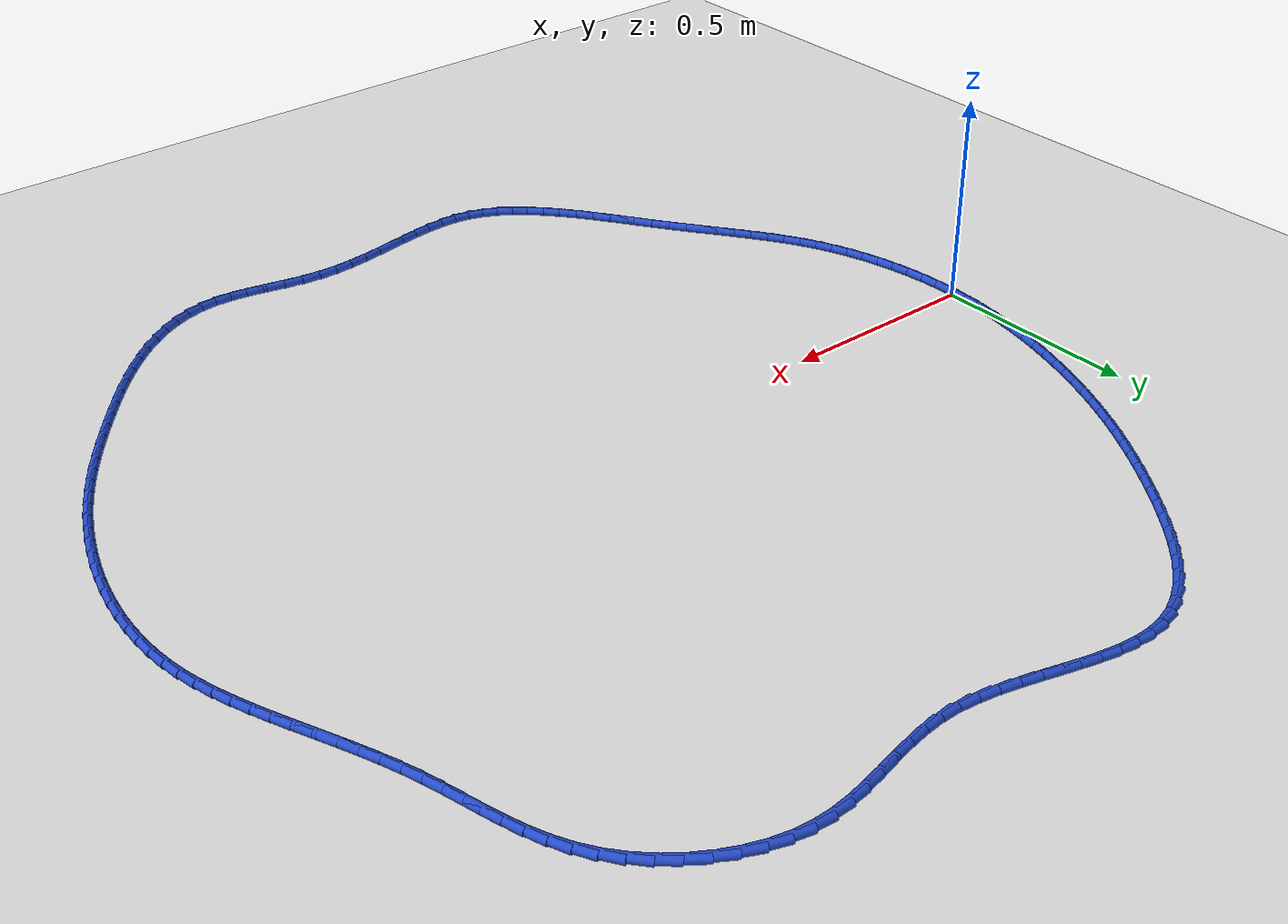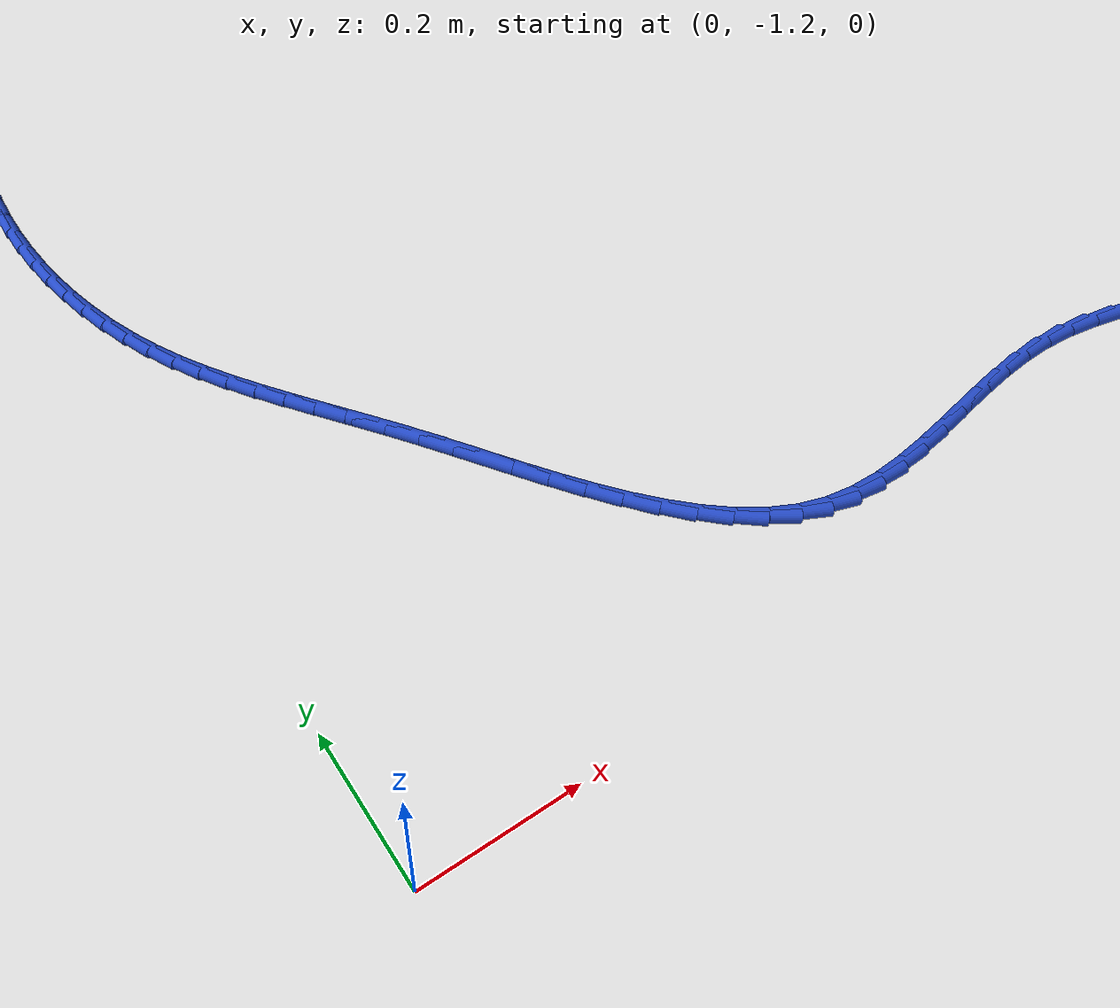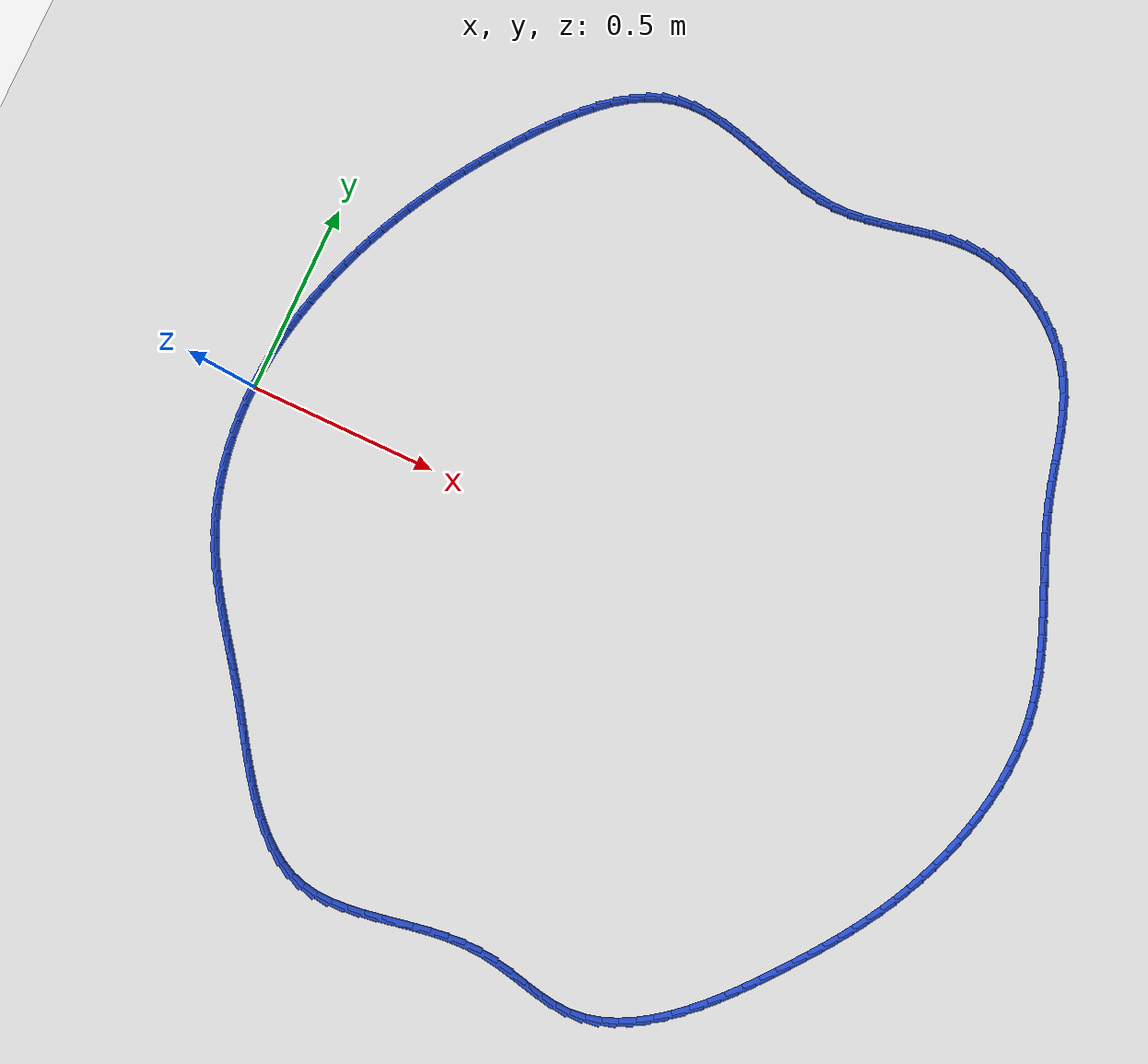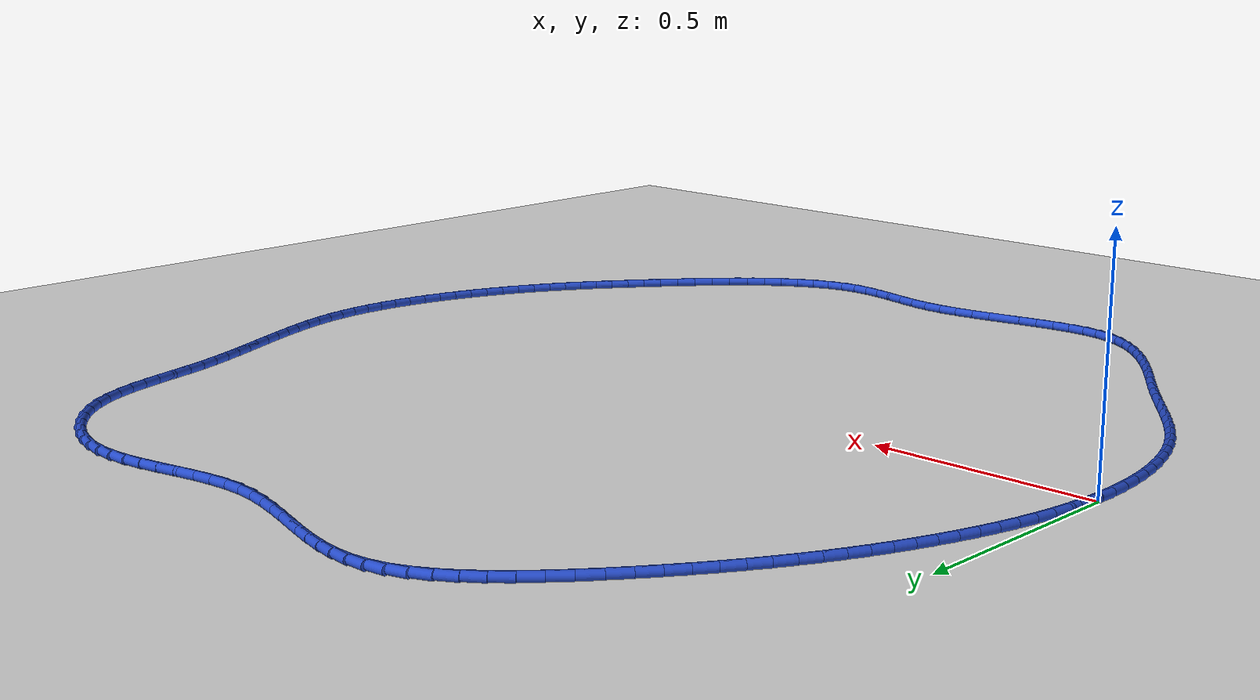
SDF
<sdf version="1.6">
 <world name="default">
  <light name="sun" type="directional">
   <pose>0 0 10 0 -0 0</pose>
   <diffuse>0.8 0.8 0.8 1</diffuse>
   <specular>0.2 0.2 0.2 1</specular>
   <attenuation>
    <range>1000</range>
    <constant>0.9</constant>
    <linear>0.01</linear>
    <quadratic>0.001</quadratic>
   </attenuation>
   <direction>-0.5 0.1 -0.9</direction>
  </light>
  <model name="ground_plane">
   <static>1</static>
   <link name="link">
    <collision name="collision">
     <geometry><plane><normal>0 0 1</normal><size>100 100</size></plane></geometry>
     <surface><friction><ode><mu>100</mu><mu2>50</mu2></ode></friction></surface>
    </collision>
    <visual name="visual">
     <cast_shadows>0</cast_shadows>
     <geometry><plane><normal>0 0 1</normal><size>100 100</size></plane></geometry>
     <material>
      <script><uri>file://media/materials/scripts/gazebo.material</uri><name>Gazebo/WhiteGlow</name></script>
     </material>
    </visual>
   </link>
  </model>
  <gravity>0 0 -9.8</gravity>
  <magnetic_field>6e-06 2.3e-05 -4.2e-05</magnetic_field>
  <atmosphere type="adiabatic"/>
  <physics name="default_physics" default="0" type="ode">
   <max_step_size>0.001</max_step_size>
   <real_time_factor>1</real_time_factor>
   <real_time_update_rate>1000</real_time_update_rate>
  </physics>
  <scene><ambient>0.4 0.4 0.4 1</ambient><background>0.7 0.7 0.7 1</background><shadows>1</shadows></scene>
  <spherical_coordinates>
   <surface_model>EARTH_WGS84</surface_model>
   <latitude_deg>0</latitude_deg>
   <longitude_deg>0</longitude_deg>
   <elevation>0</elevation>
   <heading_deg>0</heading_deg>
  </spherical_coordinates>
  <model name="line">
   <link name="link_0">
    <pose>3.9898639947466563e-17 2.7755575615628914e-17 0.01 0 1.57 1.5283468277416203</pose>
    <collision name="collision">
     <geometry><cylinder><radius>0.01</radius><length>0.08</length></cylinder></geometry>
    </collision>
    <visual name="visual">
     <material>
      <script><name>Gazebo/Blue</name><uri>file://media/materials/scripts/gazebo.material</uri></script>
     </material>
     <geometry><cylinder><radius>0.01</radius><length>0.08</length></cylinder></geometry>
    </visual>
   </link>
   <link name="link_1">
    <pose>0.0018773794262160705 0.0441996178607598 0.01 0 1.57 1.4841949896388122</pose>
    <collision name="collision">
     <geometry><cylinder><radius>0.01</radius><length>0.08</length></cylinder></geometry>
    </collision>
    <visual name="visual">
     <material>
      <script><name>Gazebo/Blue</name><uri>file://media/materials/scripts/gazebo.material</uri></script>
     </material>
     <geometry><cylinder><radius>0.01</radius><length>0.08</length></cylinder></geometry>
    </visual>
   </link>
   <link name="link_2">
    <pose>0.00569221182953699 0.08813994188575232 0.01 0 1.57 1.442375402503813</pose>
    <collision name="collision">
     <geometry><cylinder><radius>0.01</radius><length>0.08</length></cylinder></geometry>
    </collision>
    <visual name="visual">
     <material>
      <script><name>Gazebo/Blue</name><uri>file://media/materials/scripts/gazebo.material</uri></script>
     </material>
     <geometry><cylinder><radius>0.01</radius><length>0.08</length></cylinder></geometry>
    </visual>
   </link>
   <link name="link_3">
    <pose>0.01132656917750486 0.13177262444632545 0.01 0 1.57 1.402879705712286</pose>
    <collision name="collision">
     <geometry><cylinder><radius>0.01</radius><length>0.08</length></cylinder></geometry>
    </collision>
    <visual name="visual">
     <material>
      <script><name>Gazebo/Blue</name><uri>file://media/materials/scripts/gazebo.material</uri></script>
     </material>
     <geometry><cylinder><radius>0.01</radius><length>0.08</length></cylinder></geometry>
    </visual>
   </link>
   <link name="link_4">
    <pose>0.01866252343766173 0.175049317913827 0.01 0 1.57 1.3656718448897593</pose>
    <collision name="collision">
     <geometry><cylinder><radius>0.01</radius><length>0.08</length></cylinder></geometry>
    </collision>
    <visual name="visual">
     <material>
      <script><name>Gazebo/Blue</name><uri>file://media/materials/scripts/gazebo.material</uri></script>
     </material>
     <geometry><cylinder><radius>0.01</radius><length>0.08</length></cylinder></geometry>
    </visual>
   </link>
   <link name="link_5">
    <pose>0.027582146577549666 0.21792167465960488 0.01 0 1.57 1.330694869672909</pose>
    <collision name="collision">
     <geometry><cylinder><radius>0.01</radius><length>0.08</length></cylinder></geometry>
    </collision>
    <visual name="visual">
     <material>
      <script><name>Gazebo/Blue</name><uri>file://media/materials/scripts/gazebo.material</uri></script>
     </material>
     <geometry><cylinder><radius>0.01</radius><length>0.08</length></cylinder></geometry>
    </visual>
   </link>
   <link name="link_6">
    <pose>0.03796751056471074 0.26034134705500694 0.01 0 1.57 1.2978770520964877</pose>
    <collision name="collision">
     <geometry><cylinder><radius>0.01</radius><length>0.08</length></cylinder></geometry>
    </collision>
    <visual name="visual">
     <material>
      <script><name>Gazebo/Blue</name><uri>file://media/materials/scripts/gazebo.material</uri></script>
     </material>
     <geometry><cylinder><radius>0.01</radius><length>0.08</length></cylinder></geometry>
    </visual>
   </link>
   <link name="link_7">
    <pose>0.049700687366686994 0.3022599874713811 0.01 0 1.57 1.2671371870385222</pose>
    <collision name="collision">
     <geometry><cylinder><radius>0.01</radius><length>0.08</length></cylinder></geometry>
    </collision>
    <visual name="visual">
     <material>
      <script><name>Gazebo/Blue</name><uri>file://media/materials/scripts/gazebo.material</uri></script>
     </material>
     <geometry><cylinder><radius>0.01</radius><length>0.08</length></cylinder></geometry>
    </visual>
   </link>
   <link name="link_8">
    <pose>0.06266374895102049 0.34362924828007513 0.01 0 1.57 1.238389022745369</pose>
    <collision name="collision">
     <geometry><cylinder><radius>0.01</radius><length>0.08</length></cylinder></geometry>
    </collision>
    <visual name="visual">
     <material>
      <script><name>Gazebo/Blue</name><uri>file://media/materials/scripts/gazebo.material</uri></script>
     </material>
     <geometry><cylinder><radius>0.01</radius><length>0.08</length></cylinder></geometry>
    </visual>
   </link>
   <link name="link_9">
    <pose>0.07673876898450409 0.3844007832674508 0.01 0 1.57 1.2111672025673526</pose>
    <collision name="collision">
     <geometry><cylinder><radius>0.01</radius><length>0.08</length></cylinder></geometry>
    </collision>
    <visual name="visual">
     <material>
      <script><name>Gazebo/Blue</name><uri>file://media/materials/scripts/gazebo.material</uri></script>
     </material>
     <geometry><cylinder><radius>0.01</radius><length>0.08</length></cylinder></geometry>
    </visual>
   </link>
   <link name="link_10">
    <pose>0.09183300477948912 0.4245472173480202 0.01 0 1.57 1.1841548187913944</pose>
    <collision name="collision">
     <geometry><cylinder><radius>0.01</radius><length>0.08</length></cylinder></geometry>
    </collision>
    <visual name="visual">
     <material>
      <script><name>Gazebo/Blue</name><uri>file://media/materials/scripts/gazebo.material</uri></script>
     </material>
     <geometry><cylinder><radius>0.01</radius><length>0.08</length></cylinder></geometry>
    </visual>
   </link>
   <link name="link_11">
    <pose>0.1079424291087033 0.4641150512889467 0.01 0 1.57 1.157207312297957</pose>
    <collision name="collision">
     <geometry><cylinder><radius>0.01</radius><length>0.08</length></cylinder></geometry>
    </collision>
    <visual name="visual">
     <material>
      <script><name>Gazebo/Blue</name><uri>file://media/materials/scripts/gazebo.material</uri></script>
     </material>
     <geometry><cylinder><radius>0.01</radius><length>0.08</length></cylinder></geometry>
    </visual>
   </link>
   <link name="link_12">
    <pose>0.12508253987730664 0.5031670449829216 0.01 0 1.57 1.1304850856862338</pose>
    <collision name="collision">
     <geometry><cylinder><radius>0.01</radius><length>0.08</length></cylinder></geometry>
    </collision>
    <visual name="visual">
     <material>
      <script><name>Gazebo/Blue</name><uri>file://media/materials/scripts/gazebo.material</uri></script>
     </material>
     <geometry><cylinder><radius>0.01</radius><length>0.08</length></cylinder></geometry>
    </visual>
   </link>
   <link name="link_13">
    <pose>0.14326883499045895 0.541765958322636 0.01 0 1.57 1.104144897239934</pose>
    <collision name="collision">
     <geometry><cylinder><radius>0.01</radius><length>0.08</length></cylinder></geometry>
    </collision>
    <visual name="visual">
     <material>
      <script><name>Gazebo/Blue</name><uri>file://media/materials/scripts/gazebo.material</uri></script>
     </material>
     <geometry><cylinder><radius>0.01</radius><length>0.08</length></cylinder></geometry>
    </visual>
   </link>
   <link name="link_14">
    <pose>0.16251681235332044 0.5799745512007817 0.01 0 1.57 1.0783361836781882</pose>
    <collision name="collision">
     <geometry><cylinder><radius>0.01</radius><length>0.08</length></cylinder></geometry>
    </collision>
    <visual name="visual">
     <material>
      <script><name>Gazebo/Blue</name><uri>file://media/materials/scripts/gazebo.material</uri></script>
     </material>
     <geometry><cylinder><radius>0.01</radius><length>0.08</length></cylinder></geometry>
    </visual>
   </link>
   <link name="link_15">
    <pose>0.18284196987105086 0.6178555835100495 0.01 0 1.57 1.0531977779536694</pose>
    <collision name="collision">
     <geometry><cylinder><radius>0.01</radius><length>0.08</length></cylinder></geometry>
    </collision>
    <visual name="visual">
     <material>
      <script><name>Gazebo/Blue</name><uri>file://media/materials/scripts/gazebo.material</uri></script>
     </material>
     <geometry><cylinder><radius>0.01</radius><length>0.08</length></cylinder></geometry>
    </visual>
   </link>
   <link name="link_16">
    <pose>0.2042598054488104 0.6554718151431315 0.01 0 1.57 1.0288551834632929</pose>
    <collision name="collision">
     <geometry><cylinder><radius>0.01</radius><length>0.08</length></cylinder></geometry>
    </collision>
    <visual name="visual">
     <material>
      <script><name>Gazebo/Blue</name><uri>file://media/materials/scripts/gazebo.material</uri></script>
     </material>
     <geometry><cylinder><radius>0.01</radius><length>0.08</length></cylinder></geometry>
    </visual>
   </link>
   <link name="link_17">
    <pose>0.22678581699175887 0.6928860059927187 0.01 0 1.57 1.005418512661279</pose>
    <collision name="collision">
     <geometry><cylinder><radius>0.01</radius><length>0.08</length></cylinder></geometry>
    </collision>
    <visual name="visual">
     <material>
      <script><name>Gazebo/Blue</name><uri>file://media/materials/scripts/gazebo.material</uri></script>
     </material>
     <geometry><cylinder><radius>0.01</radius><length>0.08</length></cylinder></geometry>
    </visual>
   </link>
   <link name="link_18">
    <pose>0.25043550240505624 0.7301609159515021 0.01 0 1.57 0.9829811391099385</pose>
    <collision name="collision">
     <geometry><cylinder><radius>0.01</radius><length>0.08</length></cylinder></geometry>
    </collision>
    <visual name="visual">
     <material>
      <script><name>Gazebo/Blue</name><uri>file://media/materials/scripts/gazebo.material</uri></script>
     </material>
     <geometry><cylinder><radius>0.01</radius><length>0.08</length></cylinder></geometry>
    </visual>
   </link>
   <link name="link_19">
    <pose>0.2752243595938626 0.7673593049121737 0.01 0 1.57 0.9616190553494399</pose>
    <collision name="collision">
     <geometry><cylinder><radius>0.01</radius><length>0.08</length></cylinder></geometry>
    </collision>
    <visual name="visual">
     <material>
      <script><name>Gazebo/Blue</name><uri>file://media/materials/scripts/gazebo.material</uri></script>
     </material>
     <geometry><cylinder><radius>0.01</radius><length>0.08</length></cylinder></geometry>
    </visual>
   </link>
   <link name="link_20">
    <pose>0.3011678864633377 0.8045439327674245 0.01 0 1.57 0.9413908810179638</pose>
    <collision name="collision">
     <geometry><cylinder><radius>0.01</radius><length>0.08</length></cylinder></geometry>
    </collision>
    <visual name="visual">
     <material>
      <script><name>Gazebo/Blue</name><uri>file://media/materials/scripts/gazebo.material</uri></script>
     </material>
     <geometry><cylinder><radius>0.01</radius><length>0.08</length></cylinder></geometry>
    </visual>
   </link>
   <link name="link_21">
    <pose>0.3282815809186418 0.841777559409946 0.01 0 1.57 0.9218332934378984</pose>
    <collision name="collision">
     <geometry><cylinder><radius>0.01</radius><length>0.08</length></cylinder></geometry>
    </collision>
    <visual name="visual">
     <material>
      <script><name>Gazebo/Blue</name><uri>file://media/materials/scripts/gazebo.material</uri></script>
     </material>
     <geometry><cylinder><radius>0.01</radius><length>0.08</length></cylinder></geometry>
    </visual>
   </link>
   <link name="link_22">
    <pose>0.35657961992224635 0.8790820397451635 0.01 0 1.57 0.8976768743063157</pose>
    <collision name="collision">
     <geometry><cylinder><radius>0.01</radius><length>0.08</length></cylinder></geometry>
    </collision>
    <visual name="visual">
     <material>
      <script><name>Gazebo/Blue</name><uri>file://media/materials/scripts/gazebo.material</uri></script>
     </material>
     <geometry><cylinder><radius>0.01</radius><length>0.08</length></cylinder></geometry>
    </visual>
   </link>
   <link name="link_23">
    <pose>0.38606259419753153 0.9160585102461866 0.01 0 1.57 0.8653561939736665</pose>
    <collision name="collision">
     <geometry><cylinder><radius>0.01</radius><length>0.08</length></cylinder></geometry>
    </collision>
    <visual name="visual">
     <material>
      <script><name>Gazebo/Blue</name><uri>file://media/materials/scripts/gazebo.material</uri></script>
     </material>
     <geometry><cylinder><radius>0.01</radius><length>0.08</length></cylinder></geometry>
    </visual>
   </link>
   <link name="link_24">
    <pose>0.4167231023109562 0.9520606181649928 0.01 0 1.57 0.8238587374466814</pose>
    <collision name="collision">
     <geometry><cylinder><radius>0.01</radius><length>0.08</length></cylinder></geometry>
    </collision>
    <visual name="visual">
     <material>
      <script><name>Gazebo/Blue</name><uri>file://media/materials/scripts/gazebo.material</uri></script>
     </material>
     <geometry><cylinder><radius>0.01</radius><length>0.08</length></cylinder></geometry>
    </visual>
   </link>
   <link name="link_25">
    <pose>0.44855364041929546 0.9864388394828973 0.01 0 1.57 0.7717541167600173</pose>
    <collision name="collision">
     <geometry><cylinder><radius>0.01</radius><length>0.08</length></cylinder></geometry>
    </collision>
    <visual name="visual">
     <material>
      <script><name>Gazebo/Blue</name><uri>file://media/materials/scripts/gazebo.material</uri></script>
     </material>
     <geometry><cylinder><radius>0.01</radius><length>0.08</length></cylinder></geometry>
    </visual>
   </link>
   <link name="link_26">
    <pose>0.48154670467932487 1.0185436501812164 0.01 0 1.57 0.7071402901553359</pose>
    <collision name="collision">
     <geometry><cylinder><radius>0.01</radius><length>0.08</length></cylinder></geometry>
    </collision>
    <visual name="visual">
     <material>
      <script><name>Gazebo/Blue</name><uri>file://media/materials/scripts/gazebo.material</uri></script>
     </material>
     <geometry><cylinder><radius>0.01</radius><length>0.08</length></cylinder></geometry>
    </visual>
   </link>
   <link name="link_27">
    <pose>0.5156947912478198 1.0477255262412646 0.01 0 1.57 0.6276814348441409</pose>
    <collision name="collision">
     <geometry><cylinder><radius>0.01</radius><length>0.08</length></cylinder></geometry>
    </collision>
    <visual name="visual">
     <material>
      <script><name>Gazebo/Blue</name><uri>file://media/materials/scripts/gazebo.material</uri></script>
     </material>
     <geometry><cylinder><radius>0.01</radius><length>0.08</length></cylinder></geometry>
    </visual>
   </link>
   <link name="link_28">
    <pose>0.5509903962815554 1.0733349436443582 0.01 0 1.57 0.5308002408363076</pose>
    <collision name="collision">
     <geometry><cylinder><radius>0.01</radius><length>0.08</length></cylinder></geometry>
    </collision>
    <visual name="visual">
     <material>
      <script><name>Gazebo/Blue</name><uri>file://media/materials/scripts/gazebo.material</uri></script>
     </material>
     <geometry><cylinder><radius>0.01</radius><length>0.08</length></cylinder></geometry>
    </visual>
   </link>
   <link name="link_29">
    <pose>0.5874260159373074 1.0947223783718127 0.01 0 1.57 0.4141935186324031</pose>
    <collision name="collision">
     <geometry><cylinder><radius>0.01</radius><length>0.08</length></cylinder></geometry>
    </collision>
    <visual name="visual">
     <material>
      <script><name>Gazebo/Blue</name><uri>file://media/materials/scripts/gazebo.material</uri></script>
     </material>
     <geometry><cylinder><radius>0.01</radius><length>0.08</length></cylinder></geometry>
    </visual>
   </link>
   <link name="link_30">
    <pose>0.6249941463718506 1.1112383064049427 0.01 0 1.57 0.27685863087886153</pose>
    <collision name="collision">
     <geometry><cylinder><radius>0.01</radius><length>0.08</length></cylinder></geometry>
    </collision>
    <visual name="visual">
     <material>
      <script><name>Gazebo/Blue</name><uri>file://media/materials/scripts/gazebo.material</uri></script>
     </material>
     <geometry><cylinder><radius>0.01</radius><length>0.08</length></cylinder></geometry>
    </visual>
   </link>
   <link name="link_31">
    <pose>0.6636872837419605 1.1222332037250644 0.01 0 1.57 0.12503742717940666</pose>
    <collision name="collision">
     <geometry><cylinder><radius>0.01</radius><length>0.08</length></cylinder></geometry>
    </collision>
    <visual name="visual">
     <material>
      <script><name>Gazebo/Blue</name><uri>file://media/materials/scripts/gazebo.material</uri></script>
     </material>
     <geometry><cylinder><radius>0.01</radius><length>0.08</length></cylinder></geometry>
    </visual>
   </link>
   <link name="link_32">
    <pose>0.7034848335260092 1.1272354833138785 0.01 0 1.57 -0.009682901739637042</pose>
    <collision name="collision">
     <geometry><cylinder><radius>0.01</radius><length>0.08</length></cylinder></geometry>
    </collision>
    <visual name="visual">
     <material>
      <script><name>Gazebo/Blue</name><uri>file://media/materials/scripts/gazebo.material</uri></script>
     </material>
     <geometry><cylinder><radius>0.01</radius><length>0.08</length></cylinder></geometry>
    </visual>
   </link>
   <link name="link_33">
    <pose>0.7442877159498301 1.1268403806645089 0.01 0 1.57 -0.11469258326738725</pose>
    <collision name="collision">
     <geometry><cylinder><radius>0.01</radius><length>0.08</length></cylinder></geometry>
    </collision>
    <visual name="visual">
     <material>
      <script><name>Gazebo/Blue</name><uri>file://media/materials/scripts/gazebo.material</uri></script>
     </material>
     <geometry><cylinder><radius>0.01</radius><length>0.08</length></cylinder></geometry>
    </visual>
   </link>
   <link name="link_34">
    <pose>0.7859677333976002 1.122038919879541 0.01 0 1.57 -0.19127753326670552</pose>
    <collision name="collision">
     <geometry><cylinder><radius>0.01</radius><length>0.08</length></cylinder></geometry>
    </collision>
    <visual name="visual">
     <material>
      <script><name>Gazebo/Blue</name><uri>file://media/materials/scripts/gazebo.material</uri></script>
     </material>
     <geometry><cylinder><radius>0.01</radius><length>0.08</length></cylinder></geometry>
    </visual>
   </link>
   <link name="link_35">
    <pose>0.8283966403385183 1.1138227763530308 0.01 0 1.57 -0.24228257176049395</pose>
    <collision name="collision">
     <geometry><cylinder><radius>0.01</radius><length>0.08</length></cylinder></geometry>
    </collision>
    <visual name="visual">
     <material>
      <script><name>Gazebo/Blue</name><uri>file://media/materials/scripts/gazebo.material</uri></script>
     </material>
     <geometry><cylinder><radius>0.01</radius><length>0.08</length></cylinder></geometry>
    </visual>
   </link>
   <link name="link_36">
    <pose>0.8714461912417848 1.1031836254790341 0.01 0 1.57 -0.27042433900057355</pose>
    <collision name="collision">
     <geometry><cylinder><radius>0.01</radius><length>0.08</length></cylinder></geometry>
    </collision>
    <visual name="visual">
     <material>
      <script><name>Gazebo/Blue</name><uri>file://media/materials/scripts/gazebo.material</uri></script>
     </material>
     <geometry><cylinder><radius>0.01</radius><length>0.08</length></cylinder></geometry>
    </visual>
   </link>
   <link name="link_37">
    <pose>0.9149881405765988 1.091113142651607 0.01 0 1.57 -0.27757386002866985</pose>
    <collision name="collision">
     <geometry><cylinder><radius>0.01</radius><length>0.08</length></cylinder></geometry>
    </collision>
    <visual name="visual">
     <material>
      <script><name>Gazebo/Blue</name><uri>file://media/materials/scripts/gazebo.material</uri></script>
     </material>
     <geometry><cylinder><radius>0.01</radius><length>0.08</length></cylinder></geometry>
    </visual>
   </link>
   <link name="link_38">
    <pose>0.9588942428121603 1.0786030032648062 0.01 0 1.57 -0.26455155073145986</pose>
    <collision name="collision">
     <geometry><cylinder><radius>0.01</radius><length>0.08</length></cylinder></geometry>
    </collision>
    <visual name="visual">
     <material>
      <script><name>Gazebo/Blue</name><uri>file://media/materials/scripts/gazebo.material</uri></script>
     </material>
     <geometry><cylinder><radius>0.01</radius><length>0.08</length></cylinder></geometry>
    </visual>
   </link>
   <link name="link_39">
    <pose>1.0030362524176688 1.066644882712687 0.01 0 1.57 -0.23114931638908956</pose>
    <collision name="collision">
     <geometry><cylinder><radius>0.01</radius><length>0.08</length></cylinder></geometry>
    </collision>
    <visual name="visual">
     <material>
      <script><name>Gazebo/Blue</name><uri>file://media/materials/scripts/gazebo.material</uri></script>
     </material>
     <geometry><cylinder><radius>0.01</radius><length>0.08</length></cylinder></geometry>
    </visual>
   </link>
   <link name="link_40">
    <pose>1.0472859238623238 1.0562304563893061 0.01 0 1.57 -0.17629263517191962</pose>
    <collision name="collision">
     <geometry><cylinder><radius>0.01</radius><length>0.08</length></cylinder></geometry>
    </collision>
    <visual name="visual">
     <material>
      <script><name>Gazebo/Blue</name><uri>file://media/materials/scripts/gazebo.material</uri></script>
     </material>
     <geometry><cylinder><radius>0.01</radius><length>0.08</length></cylinder></geometry>
    </visual>
   </link>
   <link name="link_41">
    <pose>1.0915150116153252 1.0483513996887188 0.01 0 1.57 -0.09841034492489349</pose>
    <collision name="collision">
     <geometry><cylinder><radius>0.01</radius><length>0.08</length></cylinder></geometry>
    </collision>
    <visual name="visual">
     <material>
      <script><name>Gazebo/Blue</name><uri>file://media/materials/scripts/gazebo.material</uri></script>
     </material>
     <geometry><cylinder><radius>0.01</radius><length>0.08</length></cylinder></geometry>
    </visual>
   </link>
   <link name="link_42">
    <pose>1.1355952701458727 1.0439993880049823 0.01 0 1.57 0.0017227604798749235</pose>
    <collision name="collision">
     <geometry><cylinder><radius>0.01</radius><length>0.08</length></cylinder></geometry>
    </collision>
    <visual name="visual">
     <material>
      <script><name>Gazebo/Blue</name><uri>file://media/materials/scripts/gazebo.material</uri></script>
     </material>
     <geometry><cylinder><radius>0.01</radius><length>0.08</length></cylinder></geometry>
    </visual>
   </link>
   <link name="link_43">
    <pose>1.1794063598697995 1.0440748640936075 0.01 0 1.57 0.09612849576866987</pose>
    <collision name="collision">
     <geometry><cylinder><radius>0.01</radius><length>0.08</length></cylinder></geometry>
    </collision>
    <visual name="visual">
     <material>
      <script><name>Gazebo/Blue</name><uri>file://media/materials/scripts/gazebo.material</uri></script>
     </material>
     <geometry><cylinder><radius>0.01</radius><length>0.08</length></cylinder></geometry>
    </visual>
   </link>
   <link name="link_44">
    <pose>1.222932481623738 1.0482719005098726 0.01 0 1.57 0.1638558537596527</pose>
    <collision name="collision">
     <geometry><cylinder><radius>0.01</radius><length>0.08</length></cylinder></geometry>
    </collision>
    <visual name="visual">
     <material>
      <script><name>Gazebo/Blue</name><uri>file://media/materials/scripts/gazebo.material</uri></script>
     </material>
     <geometry><cylinder><radius>0.01</radius><length>0.08</length></cylinder></geometry>
    </visual>
   </link>
   <link name="link_45">
    <pose>1.2662318097434833 1.0554309342074606 0.01 0 1.57 0.2044519289267373</pose>
    <collision name="collision">
     <geometry><cylinder><radius>0.01</radius><length>0.08</length></cylinder></geometry>
    </collision>
    <visual name="visual">
     <material>
      <script><name>Gazebo/Blue</name><uri>file://media/materials/scripts/gazebo.material</uri></script>
     </material>
     <geometry><cylinder><radius>0.01</radius><length>0.08</length></cylinder></geometry>
    </visual>
   </link>
   <link name="link_46">
    <pose>1.309364080952772 1.0643743725756276 0.01 0 1.57 0.21842862549788306</pose>
    <collision name="collision">
     <geometry><cylinder><radius>0.01</radius><length>0.08</length></cylinder></geometry>
    </collision>
    <visual name="visual">
     <material>
      <script><name>Gazebo/Blue</name><uri>file://media/materials/scripts/gazebo.material</uri></script>
     </material>
     <geometry><cylinder><radius>0.01</radius><length>0.08</length></cylinder></geometry>
    </visual>
   </link>
   <link name="link_47">
    <pose>1.35238903197534 1.07392462300363 0.01 0 1.57 0.20597181579771012</pose>
    <collision name="collision">
     <geometry><cylinder><radius>0.01</radius><length>0.08</length></cylinder></geometry>
    </collision>
    <visual name="visual">
     <material>
      <script><name>Gazebo/Blue</name><uri>file://media/materials/scripts/gazebo.material</uri></script>
     </material>
     <geometry><cylinder><radius>0.01</radius><length>0.08</length></cylinder></geometry>
    </visual>
   </link>
   <link name="link_48">
    <pose>1.395366399534923 1.082904092880724 0.01 0 1.57 0.1666460633875939</pose>
    <collision name="collision">
     <geometry><cylinder><radius>0.01</radius><length>0.08</length></cylinder></geometry>
    </collision>
    <visual name="visual">
     <material>
      <script><name>Gazebo/Blue</name><uri>file://media/materials/scripts/gazebo.material</uri></script>
     </material>
     <geometry><cylinder><radius>0.01</radius><length>0.08</length></cylinder></geometry>
    </visual>
   </link>
   <link name="link_49">
    <pose>1.4383559203552574 1.0901351895961655 0.01 0 1.57 0.09964542662883993</pose>
    <collision name="collision">
     <geometry><cylinder><radius>0.01</radius><length>0.08</length></cylinder></geometry>
    </collision>
    <visual name="visual">
     <material>
      <script><name>Gazebo/Blue</name><uri>file://media/materials/scripts/gazebo.material</uri></script>
     </material>
     <geometry><cylinder><radius>0.01</radius><length>0.08</length></cylinder></geometry>
    </visual>
   </link>
   <link name="link_50">
    <pose>1.4814173311600782 1.0944403205392108 0.01 0 1.57 0.00466674974000229</pose>
    <collision name="collision">
     <geometry><cylinder><radius>0.01</radius><length>0.08</length></cylinder></geometry>
    </collision>
    <visual name="visual">
     <material>
      <script><name>Gazebo/Blue</name><uri>file://media/materials/scripts/gazebo.material</uri></script>
     </material>
     <geometry><cylinder><radius>0.01</radius><length>0.08</length></cylinder></geometry>
    </visual>
   </link>
   <link name="link_51">
    <pose>1.5246103686731232 1.0946418930991164 0.01 0 1.57 -0.11486640685059647</pose>
    <collision name="collision">
     <geometry><cylinder><radius>0.01</radius><length>0.08</length></cylinder></geometry>
    </collision>
    <visual name="visual">
     <material>
      <script><name>Gazebo/Blue</name><uri>file://media/materials/scripts/gazebo.material</uri></script>
     </material>
     <geometry><cylinder><radius>0.01</radius><length>0.08</length></cylinder></geometry>
    </visual>
   </link>
   <link name="link_52">
    <pose>1.5679611291450228 1.089640330276668 0.01 0 1.57 -0.23629674056166078</pose>
    <collision name="collision">
     <geometry><cylinder><radius>0.01</radius><length>0.08</length></cylinder></geometry>
    </collision>
    <visual name="visual">
     <material>
      <script><name>Gazebo/Blue</name><uri>file://media/materials/scripts/gazebo.material</uri></script>
     </material>
     <geometry><cylinder><radius>0.01</radius><length>0.08</length></cylinder></geometry>
    </visual>
   </link>
   <link name="link_53">
    <pose>1.6111005034226307 1.0792525758112463 0.01 0 1.57 -0.34832398092088296</pose>
    <collision name="collision">
     <geometry><cylinder><radius>0.01</radius><length>0.08</length></cylinder></geometry>
    </collision>
    <visual name="visual">
     <material>
      <script><name>Gazebo/Blue</name><uri>file://media/materials/scripts/gazebo.material</uri></script>
     </material>
     <geometry><cylinder><radius>0.01</radius><length>0.08</length></cylinder></geometry>
    </visual>
   </link>
   <link name="link_54">
    <pose>1.6534024338790512 1.0638914625740308 0.01 0 1.57 -0.4536945858135071</pose>
    <collision name="collision">
     <geometry><cylinder><radius>0.01</radius><length>0.08</length></cylinder></geometry>
    </collision>
    <visual name="visual">
     <material>
      <script><name>Gazebo/Blue</name><uri>file://media/materials/scripts/gazebo.material</uri></script>
     </material>
     <geometry><cylinder><radius>0.01</radius><length>0.08</length></cylinder></geometry>
    </visual>
   </link>
   <link name="link_55">
    <pose>1.6942364906973213 1.0439799629809332 0.01 0 1.57 -0.5554197858310866</pose>
    <collision name="collision">
     <geometry><cylinder><radius>0.01</radius><length>0.08</length></cylinder></geometry>
    </collision>
    <visual name="visual">
     <material>
      <script><name>Gazebo/Blue</name><uri>file://media/materials/scripts/gazebo.material</uri></script>
     </material>
     <geometry><cylinder><radius>0.01</radius><length>0.08</length></cylinder></geometry>
    </visual>
   </link>
   <link name="link_56">
    <pose>1.7329722440604782 1.0199410494478662 0.01 0 1.57 -0.6564915953322109</pose>
    <collision name="collision">
     <geometry><cylinder><radius>0.01</radius><length>0.08</length></cylinder></geometry>
    </collision>
    <visual name="visual">
     <material>
      <script><name>Gazebo/Blue</name><uri>file://media/materials/scripts/gazebo.material</uri></script>
     </material>
     <geometry><cylinder><radius>0.01</radius><length>0.08</length></cylinder></geometry>
    </visual>
   </link>
   <link name="link_57">
    <pose>1.768979264151558 0.9921976943907425 0.01 0 1.57 -0.7599134277073301</pose>
    <collision name="collision">
     <geometry><cylinder><radius>0.01</radius><length>0.08</length></cylinder></geometry>
    </collision>
    <visual name="visual">
     <material>
      <script><name>Gazebo/Blue</name><uri>file://media/materials/scripts/gazebo.material</uri></script>
     </material>
     <geometry><cylinder><radius>0.01</radius><length>0.08</length></cylinder></geometry>
    </visual>
   </link>
   <link name="link_58">
    <pose>1.8016271211535981 0.9611728702254744 0.01 0 1.57 -0.8687499168064824</pose>
    <collision name="collision">
     <geometry><cylinder><radius>0.01</radius><length>0.08</length></cylinder></geometry>
    </collision>
    <visual name="visual">
     <material>
      <script><name>Gazebo/Blue</name><uri>file://media/materials/scripts/gazebo.material</uri></script>
     </material>
     <geometry><cylinder><radius>0.01</radius><length>0.08</length></cylinder></geometry>
    </visual>
   </link>
   <link name="link_59">
    <pose>1.8302853852496346 0.9272895493679748 0.01 0 1.57 -0.9851431907706957</pose>
    <collision name="collision">
     <geometry><cylinder><radius>0.01</radius><length>0.08</length></cylinder></geometry>
    </collision>
    <visual name="visual">
     <material>
      <script><name>Gazebo/Blue</name><uri>file://media/materials/scripts/gazebo.material</uri></script>
     </material>
     <geometry><cylinder><radius>0.01</radius><length>0.08</length></cylinder></geometry>
    </visual>
   </link>
   <link name="link_60">
    <pose>1.854376003531106 0.8909690206267675 0.01 0 1.57 -1.0954290217343032</pose>
    <collision name="collision">
     <geometry><cylinder><radius>0.01</radius><length>0.08</length></cylinder></geometry>
    </collision>
    <visual name="visual">
     <material>
      <script><name>Gazebo/Blue</name><uri>file://media/materials/scripts/gazebo.material</uri></script>
     </material>
     <geometry><cylinder><radius>0.01</radius><length>0.08</length></cylinder></geometry>
    </visual>
   </link>
   <link name="link_61">
    <pose>1.8741224399110057 0.8526068087917604 0.01 0 1.57 -1.1851198841722708</pose>
    <collision name="collision">
     <geometry><cylinder><radius>0.01</radius><length>0.08</length></cylinder></geometry>
    </collision>
    <visual name="visual">
     <material>
      <script><name>Gazebo/Blue</name><uri>file://media/materials/scripts/gazebo.material</uri></script>
     </material>
     <geometry><cylinder><radius>0.01</radius><length>0.08</length></cylinder></geometry>
    </visual>
   </link>
   <link name="link_62">
    <pose>1.8903744015652888 0.8125783086410515 0.01 0 1.57 -1.2523048082926052</pose>
    <collision name="collision">
     <geometry><cylinder><radius>0.01</radius><length>0.08</length></cylinder></geometry>
    </collision>
    <visual name="visual">
     <material>
      <script><name>Gazebo/Blue</name><uri>file://media/materials/scripts/gazebo.material</uri></script>
     </material>
     <geometry><cylinder><radius>0.01</radius><length>0.08</length></cylinder></geometry>
    </visual>
   </link>
   <link name="link_63">
    <pose>1.903998247350815 0.7712583796998204 0.01 0 1.57 -1.2970002897504356</pose>
    <collision name="collision">
     <geometry><cylinder><radius>0.01</radius><length>0.08</length></cylinder></geometry>
    </collision>
    <visual name="visual">
     <material>
      <script><name>Gazebo/Blue</name><uri>file://media/materials/scripts/gazebo.material</uri></script>
     </material>
     <geometry><cylinder><radius>0.01</radius><length>0.08</length></cylinder></geometry>
    </visual>
   </link>
   <link name="link_64">
    <pose>1.9158603361244457 0.7290218814932485 0.01 0 1.57 -1.3198392782651724</pose>
    <collision name="collision">
     <geometry><cylinder><radius>0.01</radius><length>0.08</length></cylinder></geometry>
    </collision>
    <visual name="visual">
     <material>
      <script><name>Gazebo/Blue</name><uri>file://media/materials/scripts/gazebo.material</uri></script>
     </material>
     <geometry><cylinder><radius>0.01</radius><length>0.08</length></cylinder></geometry>
    </visual>
   </link>
   <link name="link_65">
    <pose>1.9268270267430412 0.6862436735465157 0.01 0 1.57 -1.3214089988809954</pose>
    <collision name="collision">
     <geometry><cylinder><radius>0.01</radius><length>0.08</length></cylinder></geometry>
    </collision>
    <visual name="visual">
     <material>
      <script><name>Gazebo/Blue</name><uri>file://media/materials/scripts/gazebo.material</uri></script>
     </material>
     <geometry><cylinder><radius>0.01</radius><length>0.08</length></cylinder></geometry>
    </visual>
   </link>
   <link name="link_66">
    <pose>1.937764678063463 0.6432986153848024 0.01 0 1.57 -1.3019454532937274</pose>
    <collision name="collision">
     <geometry><cylinder><radius>0.01</radius><length>0.08</length></cylinder></geometry>
    </collision>
    <visual name="visual">
     <material>
      <script><name>Gazebo/Blue</name><uri>file://media/materials/scripts/gazebo.material</uri></script>
     </material>
     <geometry><cylinder><radius>0.01</radius><length>0.08</length></cylinder></geometry>
    </visual>
   </link>
   <link name="link_67">
    <pose>1.9495396489425691 0.6005615665332887 0.01 0 1.57 -1.2646261209700143</pose>
    <collision name="collision">
     <geometry><cylinder><radius>0.01</radius><length>0.08</length></cylinder></geometry>
    </collision>
    <visual name="visual">
     <material>
      <script><name>Gazebo/Blue</name><uri>file://media/materials/scripts/gazebo.material</uri></script>
     </material>
     <geometry><cylinder><radius>0.01</radius><length>0.08</length></cylinder></geometry>
    </visual>
   </link>
   <link name="link_68">
    <pose>1.96288165435249 0.5583547080388547 0.01 0 1.57 -1.2287344443478352</pose>
    <collision name="collision">
     <geometry><cylinder><radius>0.01</radius><length>0.08</length></cylinder></geometry>
    </collision>
    <visual name="visual">
     <material>
      <script><name>Gazebo/Blue</name><uri>file://media/materials/scripts/gazebo.material</uri></script>
     </material>
     <geometry><cylinder><radius>0.01</radius><length>0.08</length></cylinder></geometry>
    </visual>
   </link>
   <link name="link_69">
    <pose>1.9777166047164874 0.5166903409960618 0.01 0 1.57 -1.2013833679019603</pose>
    <collision name="collision">
     <geometry><cylinder><radius>0.01</radius><length>0.08</length></cylinder></geometry>
    </collision>
    <visual name="visual">
     <material>
      <script><name>Gazebo/Blue</name><uri>file://media/materials/scripts/gazebo.material</uri></script>
     </material>
     <geometry><cylinder><radius>0.01</radius><length>0.08</length></cylinder></geometry>
    </visual>
   </link>
   <link name="link_70">
    <pose>1.9936774643392785 0.4754678309240564 0.01 0 1.57 -1.1825807462609383</pose>
    <collision name="collision">
     <geometry><cylinder><radius>0.01</radius><length>0.08</length></cylinder></geometry>
    </collision>
    <visual name="visual">
     <material>
      <script><name>Gazebo/Blue</name><uri>file://media/materials/scripts/gazebo.material</uri></script>
     </material>
     <geometry><cylinder><radius>0.01</radius><length>0.08</length></cylinder></geometry>
    </visual>
   </link>
   <link name="link_71">
    <pose>2.010396772606886 0.43458637952879803 0.01 0 1.57 -1.1723111704641578</pose>
    <collision name="collision">
     <geometry><cylinder><radius>0.01</radius><length>0.08</length></cylinder></geometry>
    </collision>
    <visual name="visual">
     <material>
      <script><name>Gazebo/Blue</name><uri>file://media/materials/scripts/gazebo.material</uri></script>
     </material>
     <geometry><cylinder><radius>0.01</radius><length>0.08</length></cylinder></geometry>
    </visual>
   </link>
   <link name="link_72">
    <pose>2.0275070689053316 0.39394518851624705 0.01 0 1.57 -1.1705875674830826</pose>
    <collision name="collision">
     <geometry><cylinder><radius>0.01</radius><length>0.08</length></cylinder></geometry>
    </collision>
    <visual name="visual">
     <material>
      <script><name>Gazebo/Blue</name><uri>file://media/materials/scripts/gazebo.material</uri></script>
     </material>
     <geometry><cylinder><radius>0.01</radius><length>0.08</length></cylinder></geometry>
    </visual>
   </link>
   <link name="link_73">
    <pose>2.0446408926206385 0.35344345959236273 0.01 0 1.57 -1.1774742670913005</pose>
    <collision name="collision">
     <geometry><cylinder><radius>0.01</radius><length>0.08</length></cylinder></geometry>
    </collision>
    <visual name="visual">
     <material>
      <script><name>Gazebo/Blue</name><uri>file://media/materials/scripts/gazebo.material</uri></script>
     </material>
     <geometry><cylinder><radius>0.01</radius><length>0.08</length></cylinder></geometry>
    </visual>
   </link>
   <link name="link_74">
    <pose>2.0614307831388285 0.3129803944631055 0.01 0 1.57 -1.1930921714082812</pose>
    <collision name="collision">
     <geometry><cylinder><radius>0.01</radius><length>0.08</length></cylinder></geometry>
    </collision>
    <visual name="visual">
     <material>
      <script><name>Gazebo/Blue</name><uri>file://media/materials/scripts/gazebo.material</uri></script>
     </material>
     <geometry><cylinder><radius>0.01</radius><length>0.08</length></cylinder></geometry>
    </visual>
   </link>
   <link name="link_75">
    <pose>2.0775092798459243 0.2724551948344349 0.01 0 1.57 -1.2176051850448366</pose>
    <collision name="collision">
     <geometry><cylinder><radius>0.01</radius><length>0.08</length></cylinder></geometry>
    </collision>
    <visual name="visual">
     <material>
      <script><name>Gazebo/Blue</name><uri>file://media/materials/scripts/gazebo.material</uri></script>
     </material>
     <geometry><cylinder><radius>0.01</radius><length>0.08</length></cylinder></geometry>
    </visual>
   </link>
   <link name="link_76">
    <pose>2.0925089221279483 0.23176706241231035 0.01 0 1.57 -1.2511855249891992</pose>
    <collision name="collision">
     <geometry><cylinder><radius>0.01</radius><length>0.08</length></cylinder></geometry>
    </collision>
    <visual name="visual">
     <material>
      <script><name>Gazebo/Blue</name><uri>file://media/materials/scripts/gazebo.material</uri></script>
     </material>
     <geometry><cylinder><radius>0.01</radius><length>0.08</length></cylinder></geometry>
    </visual>
   </link>
   <link name="link_77">
    <pose>2.1060622493709227 0.19081519890269247 0.01 0 1.57 -1.2939547211688303</pose>
    <collision name="collision">
     <geometry><cylinder><radius>0.01</radius><length>0.08</length></cylinder></geometry>
    </collision>
    <visual name="visual">
     <material>
      <script><name>Gazebo/Blue</name><uri>file://media/materials/scripts/gazebo.material</uri></script>
     </material>
     <geometry><cylinder><radius>0.01</radius><length>0.08</length></cylinder></geometry>
    </visual>
   </link>
   <link name="link_78">
    <pose>2.1178018009608706 0.14949880601154034 0.01 0 1.57 -1.3458984760475654</pose>
    <collision name="collision">
     <geometry><cylinder><radius>0.01</radius><length>0.08</length></cylinder></geometry>
    </collision>
    <visual name="visual">
     <material>
      <script><name>Gazebo/Blue</name><uri>file://media/materials/scripts/gazebo.material</uri></script>
     </material>
     <geometry><cylinder><radius>0.01</radius><length>0.08</length></cylinder></geometry>
    </visual>
   </link>
   <link name="link_79">
    <pose>2.127360116283814 0.10771708544481451 0.01 0 1.57 -1.406756580920014</pose>
    <collision name="collision">
     <geometry><cylinder><radius>0.01</radius><length>0.08</length></cylinder></geometry>
    </collision>
    <visual name="visual">
     <material>
      <script><name>Gazebo/Blue</name><uri>file://media/materials/scripts/gazebo.material</uri></script>
     </material>
     <geometry><cylinder><radius>0.01</radius><length>0.08</length></cylinder></geometry>
    </visual>
   </link>
   <link name="link_80">
    <pose>2.1343698266237463 0.0653692851292034 0.01 0 1.57 -1.473188336971283</pose>
    <collision name="collision">
     <geometry><cylinder><radius>0.01</radius><length>0.08</length></cylinder></geometry>
    </collision>
    <visual name="visual">
     <material>
      <script><name>Gazebo/Blue</name><uri>file://media/materials/scripts/gazebo.material</uri></script>
     </material>
     <geometry><cylinder><radius>0.01</radius><length>0.08</length></cylinder></geometry>
    </visual>
   </link>
   <link name="link_81">
    <pose>2.1385762341780024 0.02241132161755945 0.01 0 1.57 -1.5367360990285168</pose>
    <collision name="collision">
     <geometry><cylinder><radius>0.01</radius><length>0.08</length></cylinder></geometry>
    </collision>
    <visual name="visual">
     <material>
      <script><name>Gazebo/Blue</name><uri>file://media/materials/scripts/gazebo.material</uri></script>
     </material>
     <geometry><cylinder><radius>0.01</radius><length>0.08</length></cylinder></geometry>
    </visual>
   </link>
   <link name="link_82">
    <pose>2.140056562389448 -0.02103394641865927 0.01 0 1.57 1.5454995120149058</pose>
    <collision name="collision">
     <geometry><cylinder><radius>0.01</radius><length>0.08</length></cylinder></geometry>
    </collision>
    <visual name="visual">
     <material>
      <script><name>Gazebo/Blue</name><uri>file://media/materials/scripts/gazebo.material</uri></script>
     </material>
     <geometry><cylinder><radius>0.01</radius><length>0.08</length></cylinder></geometry>
    </visual>
   </link>
   <link name="link_83">
    <pose>2.138948853689419 -0.06481307097114308 0.01 0 1.57 1.490041009162373</pose>
    <collision name="collision">
     <geometry><cylinder><radius>0.01</radius><length>0.08</length></cylinder></geometry>
    </collision>
    <visual name="visual">
     <material>
      <script><name>Gazebo/Blue</name><uri>file://media/materials/scripts/gazebo.material</uri></script>
     </material>
     <geometry><cylinder><radius>0.01</radius><length>0.08</length></cylinder></geometry>
    </visual>
   </link>
   <link name="link_84">
    <pose>2.1353911505092515 -0.10877260403158467 0.01 0 1.57 1.4381378140270304</pose>
    <collision name="collision">
     <geometry><cylinder><radius>0.01</radius><length>0.08</length></cylinder></geometry>
    </collision>
    <visual name="visual">
     <material>
      <script><name>Gazebo/Blue</name><uri>file://media/materials/scripts/gazebo.material</uri></script>
     </material>
     <geometry><cylinder><radius>0.01</radius><length>0.08</length></cylinder></geometry>
    </visual>
   </link>
   <link name="link_85">
    <pose>2.129521495280283 -0.15275909759167597 0.01 0 1.57 1.3894200010257964</pose>
    <collision name="collision">
     <geometry><cylinder><radius>0.01</radius><length>0.08</length></cylinder></geometry>
    </collision>
    <visual name="visual">
     <material>
      <script><name>Gazebo/Blue</name><uri>file://media/materials/scripts/gazebo.material</uri></script>
     </material>
     <geometry><cylinder><radius>0.01</radius><length>0.08</length></cylinder></geometry>
    </visual>
   </link>
   <link name="link_86">
    <pose>2.12147793043385 -0.1966191036431089 0.01 0 1.57 1.343507507257233</pose>
    <collision name="collision">
     <geometry><cylinder><radius>0.01</radius><length>0.08</length></cylinder></geometry>
    </collision>
    <visual name="visual">
     <material>
      <script><name>Gazebo/Blue</name><uri>file://media/materials/scripts/gazebo.material</uri></script>
     </material>
     <geometry><cylinder><radius>0.01</radius><length>0.08</length></cylinder></geometry>
    </visual>
   </link>
   <link name="link_87">
    <pose>2.111398498401288 -0.24019917417757602 0.01 0 1.57 1.3000201977026942</pose>
    <collision name="collision">
     <geometry><cylinder><radius>0.01</radius><length>0.08</length></cylinder></geometry>
    </collision>
    <visual name="visual">
     <material>
      <script><name>Gazebo/Blue</name><uri>file://media/materials/scripts/gazebo.material</uri></script>
     </material>
     <geometry><cylinder><radius>0.01</radius><length>0.08</length></cylinder></geometry>
    </visual>
   </link>
   <link name="link_88">
    <pose>2.099421241613934 -0.28334586118676774 0.01 0 1.57 1.2585828224933822</pose>
    <collision name="collision">
     <geometry><cylinder><radius>0.01</radius><length>0.08</length></cylinder></geometry>
    </collision>
    <visual name="visual">
     <material>
      <script><name>Gazebo/Blue</name><uri>file://media/materials/scripts/gazebo.material</uri></script>
     </material>
     <geometry><cylinder><radius>0.01</radius><length>0.08</length></cylinder></geometry>
    </visual>
   </link>
   <link name="link_89">
    <pose>2.085684202503125 -0.325905716662377 0.01 0 1.57 1.2188260554733037</pose>
    <collision name="collision">
     <geometry><cylinder><radius>0.01</radius><length>0.08</length></cylinder></geometry>
    </collision>
    <visual name="visual">
     <material>
      <script><name>Gazebo/Blue</name><uri>file://media/materials/scripts/gazebo.material</uri></script>
     </material>
     <geometry><cylinder><radius>0.01</radius><length>0.08</length></cylinder></geometry>
    </visual>
   </link>
   <link name="link_90">
    <pose>2.070325423500197 -0.3677252925960953 0.01 0 1.57 1.1803845038735719</pose>
    <collision name="collision">
     <geometry><cylinder><radius>0.01</radius><length>0.08</length></cylinder></geometry>
    </collision>
    <visual name="visual">
     <material>
      <script><name>Gazebo/Blue</name><uri>file://media/materials/scripts/gazebo.material</uri></script>
     </material>
     <geometry><cylinder><radius>0.01</radius><length>0.08</length></cylinder></geometry>
    </visual>
   </link>
   <link name="link_91">
    <pose>2.053482947036486 -0.4086511409796147 0.01 0 1.57 1.1428922585203218</pose>
    <collision name="collision">
     <geometry><cylinder><radius>0.01</radius><length>0.08</length></cylinder></geometry>
    </collision>
    <visual name="visual">
     <material>
      <script><name>Gazebo/Blue</name><uri>file://media/materials/scripts/gazebo.material</uri></script>
     </material>
     <geometry><cylinder><radius>0.01</radius><length>0.08</length></cylinder></geometry>
    </visual>
   </link>
   <link name="link_92">
    <pose>2.035294815543329 -0.448529813804628 0.01 0 1.57 1.1060596783390448</pose>
    <collision name="collision">
     <geometry><cylinder><radius>0.01</radius><length>0.08</length></cylinder></geometry>
    </collision>
    <visual name="visual">
     <material>
      <script><name>Gazebo/Blue</name><uri>file://media/materials/scripts/gazebo.material</uri></script>
     </material>
     <geometry><cylinder><radius>0.01</radius><length>0.08</length></cylinder></geometry>
    </visual>
   </link>
   <link name="link_93">
    <pose>2.015889456905921 -0.48723509468058 0.01 0 1.57 1.0705007789508294</pose>
    <collision name="collision">
     <geometry><cylinder><radius>0.01</radius><length>0.08</length></cylinder></geometry>
    </collision>
    <visual name="visual">
     <material>
      <script><name>Gazebo/Blue</name><uri>file://media/materials/scripts/gazebo.material</uri></script>
     </material>
     <geometry><cylinder><radius>0.01</radius><length>0.08</length></cylinder></geometry>
    </visual>
   </link>
   <link name="link_94">
    <pose>1.9953132620136749 -0.524873123490219 0.01 0 1.57 1.037089655518106</pose>
    <collision name="collision">
     <geometry><cylinder><radius>0.01</radius><length>0.08</length></cylinder></geometry>
    </collision>
    <visual name="visual">
     <material>
      <script><name>Gazebo/Blue</name><uri>file://media/materials/scripts/gazebo.material</uri></script>
     </material>
     <geometry><cylinder><radius>0.01</radius><length>0.08</length></cylinder></geometry>
    </visual>
   </link>
   <link name="link_95">
    <pose>1.9735710687811283 -0.5616677320709373 0.01 0 1.57 1.0063798327476379</pose>
    <collision name="collision">
     <geometry><cylinder><radius>0.01</radius><length>0.08</length></cylinder></geometry>
    </collision>
    <visual name="visual">
     <material>
      <script><name>Gazebo/Blue</name><uri>file://media/materials/scripts/gazebo.material</uri></script>
     </material>
     <geometry><cylinder><radius>0.01</radius><length>0.08</length></cylinder></geometry>
    </visual>
   </link>
   <link name="link_96">
    <pose>1.9506673917016166 -0.5978436682973808 0.01 0 1.57 0.9788191739992435</pose>
    <collision name="collision">
     <geometry><cylinder><radius>0.01</radius><length>0.08</length></cylinder></geometry>
    </collision>
    <visual name="visual">
     <material>
      <script><name>Gazebo/Blue</name><uri>file://media/materials/scripts/gazebo.material</uri></script>
     </material>
     <geometry><cylinder><radius>0.01</radius><length>0.08</length></cylinder></geometry>
    </visual>
   </link>
   <link name="link_97">
    <pose>1.9266067452684816 -0.6336256800441937 0.01 0 1.57 0.9547360909347792</pose>
    <collision name="collision">
     <geometry><cylinder><radius>0.01</radius><length>0.08</length></cylinder></geometry>
    </collision>
    <visual name="visual">
     <material>
      <script><name>Gazebo/Blue</name><uri>file://media/materials/scripts/gazebo.material</uri></script>
     </material>
     <geometry><cylinder><radius>0.01</radius><length>0.08</length></cylinder></geometry>
    </visual>
   </link>
   <link name="link_98">
    <pose>1.9013936439750605 -0.6692385151860223 0.01 0 1.57 0.934334583449211</pose>
    <collision name="collision">
     <geometry><cylinder><radius>0.01</radius><length>0.08</length></cylinder></geometry>
    </collision>
    <visual name="visual">
     <material>
      <script><name>Gazebo/Blue</name><uri>file://media/materials/scripts/gazebo.material</uri></script>
     </material>
     <geometry><cylinder><radius>0.01</radius><length>0.08</length></cylinder></geometry>
    </visual>
   </link>
   <link name="link_99">
    <pose>1.8750326023146917 -0.7049069215975119 0.01 0 1.57 0.9176993403220279</pose>
    <collision name="collision">
     <geometry><cylinder><radius>0.01</radius><length>0.08</length></cylinder></geometry>
    </collision>
    <visual name="visual">
     <material>
      <script><name>Gazebo/Blue</name><uri>file://media/materials/scripts/gazebo.material</uri></script>
     </material>
     <geometry><cylinder><radius>0.01</radius><length>0.08</length></cylinder></geometry>
    </visual>
   </link>
   <link name="link_100">
    <pose>1.8475281347807133 -0.740855647153308 0.01 0 1.57 0.9044798266328412</pose>
    <collision name="collision">
     <geometry><cylinder><radius>0.01</radius><length>0.08</length></cylinder></geometry>
    </collision>
    <visual name="visual">
     <material>
      <script><name>Gazebo/Blue</name><uri>file://media/materials/scripts/gazebo.material</uri></script>
     </material>
     <geometry><cylinder><radius>0.01</radius><length>0.08</length></cylinder></geometry>
    </visual>
   </link>
   <link name="link_101">
    <pose>1.8188855009833285 -0.7772838616205846 0.01 0 1.57 0.8894356543483096</pose>
    <collision name="collision">
     <geometry><cylinder><radius>0.01</radius><length>0.08</length></cylinder></geometry>
    </collision>
    <visual name="visual">
     <material>
      <script><name>Gazebo/Blue</name><uri>file://media/materials/scripts/gazebo.material</uri></script>
     </material>
     <geometry><cylinder><radius>0.01</radius><length>0.08</length></cylinder></geometry>
    </visual>
   </link>
   <link name="link_102">
    <pose>1.7891216964506942 -0.8139878683373162 0.01 0 1.57 0.8683506349623945</pose>
    <collision name="collision">
     <geometry><cylinder><radius>0.01</radius><length>0.08</length></cylinder></geometry>
    </collision>
    <visual name="visual">
     <material>
      <script><name>Gazebo/Blue</name><uri>file://media/materials/scripts/gazebo.material</uri></script>
     </material>
     <geometry><cylinder><radius>0.01</radius><length>0.08</length></cylinder></geometry>
    </visual>
   </link>
   <link name="link_103">
    <pose>1.7582630608726735 -0.8504432075723085 0.01 0 1.57 0.8407622943882539</pose>
    <collision name="collision">
     <geometry><cylinder><radius>0.01</radius><length>0.08</length></cylinder></geometry>
    </collision>
    <visual name="visual">
     <material>
      <script><name>Gazebo/Blue</name><uri>file://media/materials/scripts/gazebo.material</uri></script>
     </material>
     <geometry><cylinder><radius>0.01</radius><length>0.08</length></cylinder></geometry>
    </visual>
   </link>
   <link name="link_104">
    <pose>1.7263361929028167 -0.8861165299808624 0.01 0 1.57 0.806032804837281</pose>
    <collision name="collision">
     <geometry><cylinder><radius>0.01</radius><length>0.08</length></cylinder></geometry>
    </collision>
    <visual name="visual">
     <material>
      <script><name>Gazebo/Blue</name><uri>file://media/materials/scripts/gazebo.material</uri></script>
     </material>
     <geometry><cylinder><radius>0.01</radius><length>0.08</length></cylinder></geometry>
    </visual>
   </link>
   <link name="link_105">
    <pose>1.6933676911946722 -0.9204744862182785 0.01 0 1.57 0.7632295218565668</pose>
    <collision name="collision">
     <geometry><cylinder><radius>0.01</radius><length>0.08</length></cylinder></geometry>
    </collision>
    <visual name="visual">
     <material>
      <script><name>Gazebo/Blue</name><uri>file://media/materials/scripts/gazebo.material</uri></script>
     </material>
     <geometry><cylinder><radius>0.01</radius><length>0.08</length></cylinder></geometry>
    </visual>
   </link>
   <link name="link_106">
    <pose>1.6593841544017898 -0.9529837269398588 0.01 0 1.57 0.7111132831733754</pose>
    <collision name="collision">
     <geometry><cylinder><radius>0.01</radius><length>0.08</length></cylinder></geometry>
    </collision>
    <visual name="visual">
     <material>
      <script><name>Gazebo/Blue</name><uri>file://media/materials/scripts/gazebo.material</uri></script>
     </material>
     <geometry><cylinder><radius>0.01</radius><length>0.08</length></cylinder></geometry>
    </visual>
   </link>
   <link name="link_107">
    <pose>1.6244121811777181 -0.9831109028009021 0.01 0 1.57 0.6481406067817213</pose>
    <collision name="collision">
     <geometry><cylinder><radius>0.01</radius><length>0.08</length></cylinder></geometry>
    </collision>
    <visual name="visual">
     <material>
      <script><name>Gazebo/Blue</name><uri>file://media/materials/scripts/gazebo.material</uri></script>
     </material>
     <geometry><cylinder><radius>0.01</radius><length>0.08</length></cylinder></geometry>
    </visual>
   </link>
   <link name="link_108">
    <pose>1.5884783701760066 -1.01032266445671 0.01 0 1.57 0.5725162226361502</pose>
    <collision name="collision">
     <geometry><cylinder><radius>0.01</radius><length>0.08</length></cylinder></geometry>
    </collision>
    <visual name="visual">
     <material>
      <script><name>Gazebo/Blue</name><uri>file://media/materials/scripts/gazebo.material</uri></script>
     </material>
     <geometry><cylinder><radius>0.01</radius><length>0.08</length></cylinder></geometry>
    </visual>
   </link>
   <link name="link_109">
    <pose>1.551609320050204 -1.0340856625625834 0.01 0 1.57 0.482358973284678</pose>
    <collision name="collision">
     <geometry><cylinder><radius>0.01</radius><length>0.08</length></cylinder></geometry>
    </collision>
    <visual name="visual">
     <material>
      <script><name>Gazebo/Blue</name><uri>file://media/materials/scripts/gazebo.material</uri></script>
     </material>
     <geometry><cylinder><radius>0.01</radius><length>0.08</length></cylinder></geometry>
    </visual>
   </link>
   <link name="link_110">
    <pose>1.5138316294538599 -1.0538665477738232 0.01 0 1.57 0.37607289792473114</pose>
    <collision name="collision">
     <geometry><cylinder><radius>0.01</radius><length>0.08</length></cylinder></geometry>
    </collision>
    <visual name="visual">
     <material>
      <script><name>Gazebo/Blue</name><uri>file://media/materials/scripts/gazebo.material</uri></script>
     </material>
     <geometry><cylinder><radius>0.01</radius><length>0.08</length></cylinder></geometry>
    </visual>
   </link>
   <link name="link_111">
    <pose>1.4751718970405223 -1.0691319707457299 0.01 0 1.57 0.2530085092322819</pose>
    <collision name="collision">
     <geometry><cylinder><radius>0.01</radius><length>0.08</length></cylinder></geometry>
    </collision>
    <visual name="visual">
     <material>
      <script><name>Gazebo/Blue</name><uri>file://media/materials/scripts/gazebo.material</uri></script>
     </material>
     <geometry><cylinder><radius>0.01</radius><length>0.08</length></cylinder></geometry>
    </visual>
   </link>
   <link name="link_112">
    <pose>1.435656721463742 -1.0793485821336042 0.01 0 1.57 0.11437197226093442</pose>
    <collision name="collision">
     <geometry><cylinder><radius>0.01</radius><length>0.08</length></cylinder></geometry>
    </collision>
    <visual name="visual">
     <material>
      <script><name>Gazebo/Blue</name><uri>file://media/materials/scripts/gazebo.material</uri></script>
     </material>
     <geometry><cylinder><radius>0.01</radius><length>0.08</length></cylinder></geometry>
    </visual>
   </link>
   <link name="link_113">
    <pose>1.3953127013770672 -1.083983032592747 0.01 0 1.57 -0.02922576626225455</pose>
    <collision name="collision">
     <geometry><cylinder><radius>0.01</radius><length>0.08</length></cylinder></geometry>
    </collision>
    <visual name="visual">
     <material>
      <script><name>Gazebo/Blue</name><uri>file://media/materials/scripts/gazebo.material</uri></script>
     </material>
     <geometry><cylinder><radius>0.01</radius><length>0.08</length></cylinder></geometry>
    </visual>
   </link>
   <link name="link_114">
    <pose>1.3541679296325253 -1.0827802026274254 0.01 0 1.57 -0.13690342467669944</pose>
    <collision name="collision">
     <geometry><cylinder><radius>0.01</radius><length>0.08</length></cylinder></geometry>
    </collision>
    <visual name="visual">
     <material>
      <script><name>Gazebo/Blue</name><uri>file://media/materials/scripts/gazebo.material</uri></script>
     </material>
     <geometry><cylinder><radius>0.01</radius><length>0.08</length></cylinder></geometry>
    </visual>
   </link>
   <link name="link_115">
    <pose>1.3122586706050459 -1.0770065654998742 0.01 0 1.57 -0.19815099363750627</pose>
    <collision name="collision">
     <geometry><cylinder><radius>0.01</radius><length>0.08</length></cylinder></geometry>
    </collision>
    <visual name="visual">
     <material>
      <script><name>Gazebo/Blue</name><uri>file://media/materials/scripts/gazebo.material</uri></script>
     </material>
     <geometry><cylinder><radius>0.01</radius><length>0.08</length></cylinder></geometry>
    </visual>
   </link>
   <link name="link_116">
    <pose>1.2696239679964256 -1.0684461239075382 0.01 0 1.57 -0.21725854134529035</pose>
    <collision name="collision">
     <geometry><cylinder><radius>0.01</radius><length>0.08</length></cylinder></geometry>
    </collision>
    <visual name="visual">
     <material>
      <script><name>Gazebo/Blue</name><uri>file://media/materials/scripts/gazebo.material</uri></script>
     </material>
     <geometry><cylinder><radius>0.01</radius><length>0.08</length></cylinder></geometry>
    </visual>
   </link>
   <link name="link_117">
    <pose>1.2263028678162993 -1.0588833102827018 0.01 0 1.57 -0.19711262413635403</pose>
    <collision name="collision">
     <geometry><cylinder><radius>0.01</radius><length>0.08</length></cylinder></geometry>
    </collision>
    <visual name="visual">
     <material>
      <script><name>Gazebo/Blue</name><uri>file://media/materials/scripts/gazebo.material</uri></script>
     </material>
     <geometry><cylinder><radius>0.01</radius><length>0.08</length></cylinder></geometry>
    </visual>
   </link>
   <link name="link_118">
    <pose>1.182334416074301 -1.0501025570576494 0.01 0 1.57 -0.1385131578281251</pose>
    <collision name="collision">
     <geometry><cylinder><radius>0.01</radius><length>0.08</length></cylinder></geometry>
    </collision>
    <visual name="visual">
     <material>
      <script><name>Gazebo/Blue</name><uri>file://media/materials/scripts/gazebo.material</uri></script>
     </material>
     <geometry><cylinder><radius>0.01</radius><length>0.08</length></cylinder></geometry>
    </visual>
   </link>
   <link name="link_119">
    <pose>1.1377576587800642 -1.0438882966646648 0.01 0 1.57 -0.04579712752888623</pose>
    <collision name="collision">
     <geometry><cylinder><radius>0.01</radius><length>0.08</length></cylinder></geometry>
    </collision>
    <visual name="visual">
     <material>
      <script><name>Gazebo/Blue</name><uri>file://media/materials/scripts/gazebo.material</uri></script>
     </material>
     <geometry><cylinder><radius>0.01</radius><length>0.08</length></cylinder></geometry>
    </visual>
   </link>
   <link name="link_120">
    <pose>1.0926255640150542 -1.0418199301147644 0.01 0 1.57 0.04286659156641538</pose>
    <collision name="collision">
     <geometry><cylinder><radius>0.01</radius><length>0.08</length></cylinder></geometry>
    </collision>
    <visual name="visual">
     <material>
      <script><name>Gazebo/Blue</name><uri>file://media/materials/scripts/gazebo.material</uri></script>
     </material>
     <geometry><cylinder><radius>0.01</radius><length>0.08</length></cylinder></geometry>
    </visual>
   </link>
   <link name="link_121">
    <pose>1.0471068390325482 -1.043772358745349 0.01 0 1.57 0.10909606365564191</pose>
    <collision name="collision">
     <geometry><cylinder><radius>0.01</radius><length>0.08</length></cylinder></geometry>
    </collision>
    <visual name="visual">
     <material>
      <script><name>Gazebo/Blue</name><uri>file://media/materials/scripts/gazebo.material</uri></script>
     </material>
     <geometry><cylinder><radius>0.01</radius><length>0.08</length></cylinder></geometry>
    </visual>
   </link>
   <link name="link_122">
    <pose>1.0014275568383504 -1.0487756540498963 0.01 0 1.57 0.15394978121453762</pose>
    <collision name="collision">
     <geometry><cylinder><radius>0.01</radius><length>0.08</length></cylinder></geometry>
    </collision>
    <visual name="visual">
     <material>
      <script><name>Gazebo/Blue</name><uri>file://media/materials/scripts/gazebo.material</uri></script>
     </material>
     <geometry><cylinder><radius>0.01</radius><length>0.08</length></cylinder></geometry>
    </visual>
   </link>
   <link name="link_123">
    <pose>0.9558142019304738 -1.0558538274444929 0.01 0 1.57 0.17850524806187737</pose>
    <collision name="collision">
     <geometry><cylinder><radius>0.01</radius><length>0.08</length></cylinder></geometry>
    </collision>
    <visual name="visual">
     <material>
      <script><name>Gazebo/Blue</name><uri>file://media/materials/scripts/gazebo.material</uri></script>
     </material>
     <geometry><cylinder><radius>0.01</radius><length>0.08</length></cylinder></geometry>
    </visual>
   </link>
   <link name="link_124">
    <pose>0.9104932588069325 -1.0640308903452247 0.01 0 1.57 0.18318178289636622</pose>
    <collision name="collision">
     <geometry><cylinder><radius>0.01</radius><length>0.08</length></cylinder></geometry>
    </collision>
    <visual name="visual">
     <material>
      <script><name>Gazebo/Blue</name><uri>file://media/materials/scripts/gazebo.material</uri></script>
     </material>
     <geometry><cylinder><radius>0.01</radius><length>0.08</length></cylinder></geometry>
    </visual>
   </link>
   <link name="link_125">
    <pose>0.86569121196574 -1.0723308541681773 0.01 0 1.57 0.16744676415221071</pose>
    <collision name="collision">
     <geometry><cylinder><radius>0.01</radius><length>0.08</length></cylinder></geometry>
    </collision>
    <visual name="visual">
     <material>
      <script><name>Gazebo/Blue</name><uri>file://media/materials/scripts/gazebo.material</uri></script>
     </material>
     <geometry><cylinder><radius>0.01</radius><length>0.08</length></cylinder></geometry>
    </visual>
   </link>
   <link name="link_126">
    <pose>0.8216345459049097 -1.0797777303294378 0.01 0 1.57 0.12965788135434847</pose>
    <collision name="collision">
     <geometry><cylinder><radius>0.01</radius><length>0.08</length></cylinder></geometry>
    </collision>
    <visual name="visual">
     <material>
      <script><name>Gazebo/Blue</name><uri>file://media/materials/scripts/gazebo.material</uri></script>
     </material>
     <geometry><cylinder><radius>0.01</radius><length>0.08</length></cylinder></geometry>
    </visual>
   </link>
   <link name="link_127">
    <pose>0.7785497451224563 -1.0853955302450913 0.01 0 1.57 0.06705076665568271</pose>
    <collision name="collision">
     <geometry><cylinder><radius>0.01</radius><length>0.08</length></cylinder></geometry>
    </collision>
    <visual name="visual">
     <material>
      <script><name>Gazebo/Blue</name><uri>file://media/materials/scripts/gazebo.material</uri></script>
     </material>
     <geometry><cylinder><radius>0.01</radius><length>0.08</length></cylinder></geometry>
    </visual>
   </link>
   <link name="link_128">
    <pose>0.7366632941163939 -1.0882082653312246 0.01 0 1.57 -0.023927208238121087</pose>
    <collision name="collision">
     <geometry><cylinder><radius>0.01</radius><length>0.08</length></cylinder></geometry>
    </collision>
    <visual name="visual">
     <material>
      <script><name>Gazebo/Blue</name><uri>file://media/materials/scripts/gazebo.material</uri></script>
     </material>
     <geometry><cylinder><radius>0.01</radius><length>0.08</length></cylinder></geometry>
    </visual>
   </link>
   <link name="link_129">
    <pose>0.6962016773847349 -1.0872399470039222 0.01 0 1.57 -0.14646528519270366</pose>
    <collision name="collision">
     <geometry><cylinder><radius>0.01</radius><length>0.08</length></cylinder></geometry>
    </collision>
    <visual name="visual">
     <material>
      <script><name>Gazebo/Blue</name><uri>file://media/materials/scripts/gazebo.material</uri></script>
     </material>
     <geometry><cylinder><radius>0.01</radius><length>0.08</length></cylinder></geometry>
    </visual>
   </link>
   <link name="link_130">
    <pose>0.6573913794254941 -1.0815145866792717 0.01 0 1.57 -0.2989712120661296</pose>
    <collision name="collision">
     <geometry><cylinder><radius>0.01</radius><length>0.08</length></cylinder></geometry>
    </collision>
    <visual name="visual">
     <material>
      <script><name>Gazebo/Blue</name><uri>file://media/materials/scripts/gazebo.material</uri></script>
     </material>
     <geometry><cylinder><radius>0.01</radius><length>0.08</length></cylinder></geometry>
    </visual>
   </link>
   <link name="link_131">
    <pose>0.6204410992648136 -1.0701261638770434 0.01 0 1.57 -0.45217458029320334</pose>
    <collision name="collision">
     <geometry><cylinder><radius>0.01</radius><length>0.08</length></cylinder></geometry>
    </collision>
    <visual name="visual">
     <material>
      <script><name>Gazebo/Blue</name><uri>file://media/materials/scripts/gazebo.material</uri></script>
     </material>
     <geometry><cylinder><radius>0.01</radius><length>0.08</length></cylinder></geometry>
    </visual>
   </link>
   <link name="link_132">
    <pose>0.5853300793891812 -1.0530713408838472 0.01 0 1.57 -0.5837557268887612</pose>
    <collision name="collision">
     <geometry><cylinder><radius>0.01</radius><length>0.08</length></cylinder></geometry>
    </collision>
    <visual name="visual">
     <material>
      <script><name>Gazebo/Blue</name><uri>file://media/materials/scripts/gazebo.material</uri></script>
     </material>
     <geometry><cylinder><radius>0.01</radius><length>0.08</length></cylinder></geometry>
    </visual>
   </link>
   <link name="link_133">
    <pose>0.5518779813591549 -1.0309745718634324 0.01 0 1.57 -0.6920425859428436</pose>
    <collision name="collision">
     <geometry><cylinder><radius>0.01</radius><length>0.08</length></cylinder></geometry>
    </collision>
    <visual name="visual">
     <material>
      <script><name>Gazebo/Blue</name><uri>file://media/materials/scripts/gazebo.material</uri></script>
     </material>
     <geometry><cylinder><radius>0.01</radius><length>0.08</length></cylinder></geometry>
    </visual>
   </link>
   <link name="link_134">
    <pose>0.5199012367486506 -1.0044730177574073 0.01 0 1.57 -0.7785770527535949</pose>
    <collision name="collision">
     <geometry><cylinder><radius>0.01</radius><length>0.08</length></cylinder></geometry>
    </collision>
    <visual name="visual">
     <material>
      <script><name>Gazebo/Blue</name><uri>file://media/materials/scripts/gazebo.material</uri></script>
     </material>
     <geometry><cylinder><radius>0.01</radius><length>0.08</length></cylinder></geometry>
    </visual>
   </link>
   <link name="link_135">
    <pose>0.48921627713158505 -0.9742038395073833 0.01 0 1.57 -0.8460274464922944</pose>
    <collision name="collision">
     <geometry><cylinder><radius>0.01</radius><length>0.08</length></cylinder></geometry>
    </collision>
    <visual name="visual">
     <material>
      <script><name>Gazebo/Blue</name><uri>file://media/materials/scripts/gazebo.material</uri></script>
     </material>
     <geometry><cylinder><radius>0.01</radius><length>0.08</length></cylinder></geometry>
    </visual>
   </link>
   <link name="link_136">
    <pose>0.459639534081874 -0.9408041980549696 0.01 0 1.57 -0.8971139655710966</pose>
    <collision name="collision">
     <geometry><cylinder><radius>0.01</radius><length>0.08</length></cylinder></geometry>
    </collision>
    <visual name="visual">
     <material>
      <script><name>Gazebo/Blue</name><uri>file://media/materials/scripts/gazebo.material</uri></script>
     </material>
     <geometry><cylinder><radius>0.01</radius><length>0.08</length></cylinder></geometry>
    </visual>
   </link>
   <link name="link_137">
    <pose>0.43098743917343524 -0.9049112543417779 0.01 0 1.57 -0.9341250803602491</pose>
    <collision name="collision">
     <geometry><cylinder><radius>0.01</radius><length>0.08</length></cylinder></geometry>
    </collision>
    <visual name="visual">
     <material>
      <script><name>Gazebo/Blue</name><uri>file://media/materials/scripts/gazebo.material</uri></script>
     </material>
     <geometry><cylinder><radius>0.01</radius><length>0.08</length></cylinder></geometry>
    </visual>
   </link>
   <link name="link_138">
    <pose>0.4030764239801844 -0.8671621693094175 0.01 0 1.57 -0.9587650643279078</pose>
    <collision name="collision">
     <geometry><cylinder><radius>0.01</radius><length>0.08</length></cylinder></geometry>
    </collision>
    <visual name="visual">
     <material>
      <script><name>Gazebo/Blue</name><uri>file://media/materials/scripts/gazebo.material</uri></script>
     </material>
     <geometry><cylinder><radius>0.01</radius><length>0.08</length></cylinder></geometry>
    </visual>
   </link>
   <link name="link_139">
    <pose>0.3757229200760379 -0.8281941038994989 0.01 0 1.57 -0.972140476639527</pose>
    <collision name="collision">
     <geometry><cylinder><radius>0.01</radius><length>0.08</length></cylinder></geometry>
    </collision>
    <visual name="visual">
     <material>
      <script><name>Gazebo/Blue</name><uri>file://media/materials/scripts/gazebo.material</uri></script>
     </material>
     <geometry><cylinder><radius>0.01</radius><length>0.08</length></cylinder></geometry>
    </visual>
   </link>
   <link name="link_140">
    <pose>0.3487433590349124 -0.7886442190536322 0.01 0 1.57 -0.9747824039818462</pose>
    <collision name="collision">
     <geometry><cylinder><radius>0.01</radius><length>0.08</length></cylinder></geometry>
    </collision>
    <visual name="visual">
     <material>
      <script><name>Gazebo/Blue</name><uri>file://media/materials/scripts/gazebo.material</uri></script>
     </material>
     <geometry><cylinder><radius>0.01</radius><length>0.08</length></cylinder></geometry>
    </visual>
   </link>
   <link name="link_141">
    <pose>0.3219541724307236 -0.7491496757134268 0.01 0 1.57 -0.966656713030123</pose>
    <collision name="collision">
     <geometry><cylinder><radius>0.01</radius><length>0.08</length></cylinder></geometry>
    </collision>
    <visual name="visual">
     <material>
      <script><name>Gazebo/Blue</name><uri>file://media/materials/scripts/gazebo.material</uri></script>
     </material>
     <geometry><cylinder><radius>0.01</radius><length>0.08</length></cylinder></geometry>
    </visual>
   </link>
   <link name="link_142">
    <pose>0.2951717918373892 -0.7103476348204947 0.01 0 1.57 -0.9496889760862077</pose>
    <collision name="collision">
     <geometry><cylinder><radius>0.01</radius><length>0.08</length></cylinder></geometry>
    </collision>
    <visual name="visual">
     <material>
      <script><name>Gazebo/Blue</name><uri>file://media/materials/scripts/gazebo.material</uri></script>
     </material>
     <geometry><cylinder><radius>0.01</radius><length>0.08</length></cylinder></geometry>
    </visual>
   </link>
   <link name="link_143">
    <pose>0.26826969177278914 -0.6727529247553911 0.01 0 1.57 -0.9365566088528425</pose>
    <collision name="collision">
     <geometry><cylinder><radius>0.01</radius><length>0.08</length></cylinder></geometry>
    </collision>
    <visual name="visual">
     <material>
      <script><name>Gazebo/Blue</name><uri>file://media/materials/scripts/gazebo.material</uri></script>
     </material>
     <geometry><cylinder><radius>0.01</radius><length>0.08</length></cylinder></geometry>
    </visual>
   </link>
   <link name="link_144">
    <pose>0.24141599008849057 -0.6362484907751431 0.01 0 1.57 -0.9319435686961882</pose>
    <collision name="collision">
     <geometry><cylinder><radius>0.01</radius><length>0.08</length></cylinder></geometry>
    </collision>
    <visual name="visual">
     <material>
      <script><name>Gazebo/Blue</name><uri>file://media/materials/scripts/gazebo.material</uri></script>
     </material>
     <geometry><cylinder><radius>0.01</radius><length>0.08</length></cylinder></geometry>
    </visual>
   </link>
   <link name="link_145">
    <pose>0.21487365815322115 -0.6005138581715237 0.01 0 1.57 -0.936354410888569</pose>
    <collision name="collision">
     <geometry><cylinder><radius>0.01</radius><length>0.08</length></cylinder></geometry>
    </collision>
    <visual name="visual">
     <material>
      <script><name>Gazebo/Blue</name><uri>file://media/materials/scripts/gazebo.material</uri></script>
     </material>
     <geometry><cylinder><radius>0.01</radius><length>0.08</length></cylinder></geometry>
    </visual>
   </link>
   <link name="link_146">
    <pose>0.1889057128357319 -0.565228454658339 0.01 0 1.57 -0.9501969839485154</pose>
    <collision name="collision">
     <geometry><cylinder><radius>0.01</radius><length>0.08</length></cylinder></geometry>
    </collision>
    <visual name="visual">
     <material>
      <script><name>Gazebo/Blue</name><uri>file://media/materials/scripts/gazebo.material</uri></script>
     </material>
     <geometry><cylinder><radius>0.01</radius><length>0.08</length></cylinder></geometry>
    </visual>
   </link>
   <link name="link_147">
    <pose>0.16377517100477518 -0.5300717079493966 0.01 0 1.57 -0.9737544903194051</pose>
    <collision name="collision">
     <geometry><cylinder><radius>0.01</radius><length>0.08</length></cylinder></geometry>
    </collision>
    <visual name="visual">
     <material>
      <script><name>Gazebo/Blue</name><uri>file://media/materials/scripts/gazebo.material</uri></script>
     </material>
     <geometry><cylinder><radius>0.01</radius><length>0.08</length></cylinder></geometry>
    </visual>
   </link>
   <link name="link_148">
    <pose>0.13974504952910188 -0.494723045758503 0.01 0 1.57 -1.0071305640242507</pose>
    <collision name="collision">
     <geometry><cylinder><radius>0.01</radius><length>0.08</length></cylinder></geometry>
    </collision>
    <visual name="visual">
     <material>
      <script><name>Gazebo/Blue</name><uri>file://media/materials/scripts/gazebo.material</uri></script>
     </material>
     <geometry><cylinder><radius>0.01</radius><length>0.08</length></cylinder></geometry>
    </visual>
   </link>
   <link name="link_149">
    <pose>0.11707836527746356 -0.45886189579946435 0.01 0 1.57 -1.0501700351057892</pose>
    <collision name="collision">
     <geometry><cylinder><radius>0.01</radius><length>0.08</length></cylinder></geometry>
    </collision>
    <visual name="visual">
     <material>
      <script><name>Gazebo/Blue</name><uri>file://media/materials/scripts/gazebo.material</uri></script>
     </material>
     <geometry><cylinder><radius>0.01</radius><length>0.08</length></cylinder></geometry>
    </visual>
   </link>
   <link name="link_150">
    <pose>0.09603813511861155 -0.4221676857860876 0.01 0 1.57 -1.102365485422863</pose>
    <collision name="collision">
     <geometry><cylinder><radius>0.01</radius><length>0.08</length></cylinder></geometry>
    </collision>
    <visual name="visual">
     <material>
      <script><name>Gazebo/Blue</name><uri>file://media/materials/scripts/gazebo.material</uri></script>
     </material>
     <geometry><cylinder><radius>0.01</radius><length>0.08</length></cylinder></geometry>
    </visual>
   </link>
   <link name="link_151">
    <pose>0.076887375921297 -0.3843198434321785 0.01 0 1.57 -1.161216630564479</pose>
    <collision name="collision">
     <geometry><cylinder><radius>0.01</radius><length>0.08</length></cylinder></geometry>
    </collision>
    <visual name="visual">
     <material>
      <script><name>Gazebo/Blue</name><uri>file://media/materials/scripts/gazebo.material</uri></script>
     </material>
     <geometry><cylinder><radius>0.01</radius><length>0.08</length></cylinder></geometry>
    </visual>
   </link>
   <link name="link_152">
    <pose>0.0598488467542835 -0.34507245999419717 0.01 0 1.57 -1.2189862209661466</pose>
    <collision name="collision">
     <geometry><cylinder><radius>0.01</radius><length>0.08</length></cylinder></geometry>
    </collision>
    <visual name="visual">
     <material>
      <script><name>Gazebo/Blue</name><uri>file://media/materials/scripts/gazebo.material</uri></script>
     </material>
     <geometry><cylinder><radius>0.01</radius><length>0.08</length></cylinder></geometry>
    </visual>
   </link>
   <link name="link_153">
    <pose>0.04496238914289955 -0.30451887208750783 0.01 0 1.57 -1.2739449715595812</pose>
    <collision name="collision">
     <geometry><cylinder><radius>0.01</radius><length>0.08</length></cylinder></geometry>
    </collision>
    <visual name="visual">
     <material>
      <script><name>Gazebo/Blue</name><uri>file://media/materials/scripts/gazebo.material</uri></script>
     </material>
     <geometry><cylinder><radius>0.01</radius><length>0.08</length></cylinder></geometry>
    </visual>
   </link>
   <link name="link_154">
    <pose>0.0322159198345299 -0.2628487178609385 0.01 0 1.57 -1.326496117661075</pose>
    <collision name="collision">
     <geometry><cylinder><radius>0.01</radius><length>0.08</length></cylinder></geometry>
    </collision>
    <visual name="visual">
     <material>
      <script><name>Gazebo/Blue</name><uri>file://media/materials/scripts/gazebo.material</uri></script>
     </material>
     <geometry><cylinder><radius>0.01</radius><length>0.08</length></cylinder></geometry>
    </visual>
   </link>
   <link name="link_155">
    <pose>0.021597352072967174 -0.2202516419612026 0.01 0 1.57 -1.3770449823187432</pose>
    <collision name="collision">
     <geometry><cylinder><radius>0.01</radius><length>0.08</length></cylinder></geometry>
    </collision>
    <visual name="visual">
     <material>
      <script><name>Gazebo/Blue</name><uri>file://media/materials/scripts/gazebo.material</uri></script>
     </material>
     <geometry><cylinder><radius>0.01</radius><length>0.08</length></cylinder></geometry>
    </visual>
   </link>
   <link name="link_156">
    <pose>0.013094599102003873 -0.1769172890350129 0.01 0 1.57 -1.4259934514987012</pose>
    <collision name="collision">
     <geometry><cylinder><radius>0.01</radius><length>0.08</length></cylinder></geometry>
    </collision>
    <visual name="visual">
     <material>
      <script><name>Gazebo/Blue</name><uri>file://media/materials/scripts/gazebo.material</uri></script>
     </material>
     <geometry><cylinder><radius>0.01</radius><length>0.08</length></cylinder></geometry>
    </visual>
   </link>
   <link name="link_157">
    <pose>0.006695574165432967 -0.13303530372908465 0.01 0 1.57 -1.4737381852390594</pose>
    <collision name="collision">
     <geometry><cylinder><radius>0.01</radius><length>0.08</length></cylinder></geometry>
    </collision>
    <visual name="visual">
     <material>
      <script><name>Gazebo/Blue</name><uri>file://media/materials/scripts/gazebo.material</uri></script>
     </material>
     <geometry><cylinder><radius>0.01</radius><length>0.08</length></cylinder></geometry>
    </visual>
   </link>
   <link name="link_158">
    <pose>0.0023881905070469297 -0.08879533069013071 0.01 0 1.57 -1.5206714131311405</pose>
    <collision name="collision">
     <geometry><cylinder><radius>0.01</radius><length>0.08</length></cylinder></geometry>
    </collision>
    <visual name="visual">
     <material>
      <script><name>Gazebo/Blue</name><uri>file://media/materials/scripts/gazebo.material</uri></script>
     </material>
     <geometry><cylinder><radius>0.01</radius><length>0.08</length></cylinder></geometry>
    </visual>
   </link>
   <link name="link_159">
    <pose>0.00016036137063840748 -0.04438701456486471 0.01 0 1.57 -1.5671835433148629</pose>
    <collision name="collision">
     <geometry><cylinder><radius>0.01</radius><length>0.08</length></cylinder></geometry>
    </collision>
    <visual name="visual">
     <material>
      <script><name>Gazebo/Blue</name><uri>file://media/materials/scripts/gazebo.material</uri></script>
     </material>
     <geometry><cylinder><radius>0.01</radius><length>0.08</length></cylinder></geometry>
    </visual>
   </link>
   <link name="link_160">
    <pose>4.5102810375396984e-17 -1.942890293094024e-16 0.01 0 1.57 1.5279256364566964</pose>
    <collision name="collision">
     <geometry><cylinder><radius>0.01</radius><length>0.08</length></cylinder></geometry>
    </collision>
    <visual name="visual">
     <material>
      <script><name>Gazebo/Blue</name><uri>file://media/materials/scripts/gazebo.material</uri></script>
     </material>
     <geometry><cylinder><radius>0.01</radius><length>0.08</length></cylinder></geometry>
    </visual>
   </link>
   <link name="link_161">
    <pose>0.001895019638924543 0.044176068357749974 0.01 0 1.57 1.5279256364566962</pose>
    <collision name="collision">
     <geometry><cylinder><radius>0.01</radius><length>0.08</length></cylinder></geometry>
    </collision>
    <visual name="visual">
     <material>
      <script><name>Gazebo/Blue</name><uri>file://media/materials/scripts/gazebo.material</uri></script>
     </material>
     <geometry><cylinder><radius>0.01</radius><length>0.08</length></cylinder></geometry>
    </visual>
   </link>
  </model>
 </world>
</sdf>
